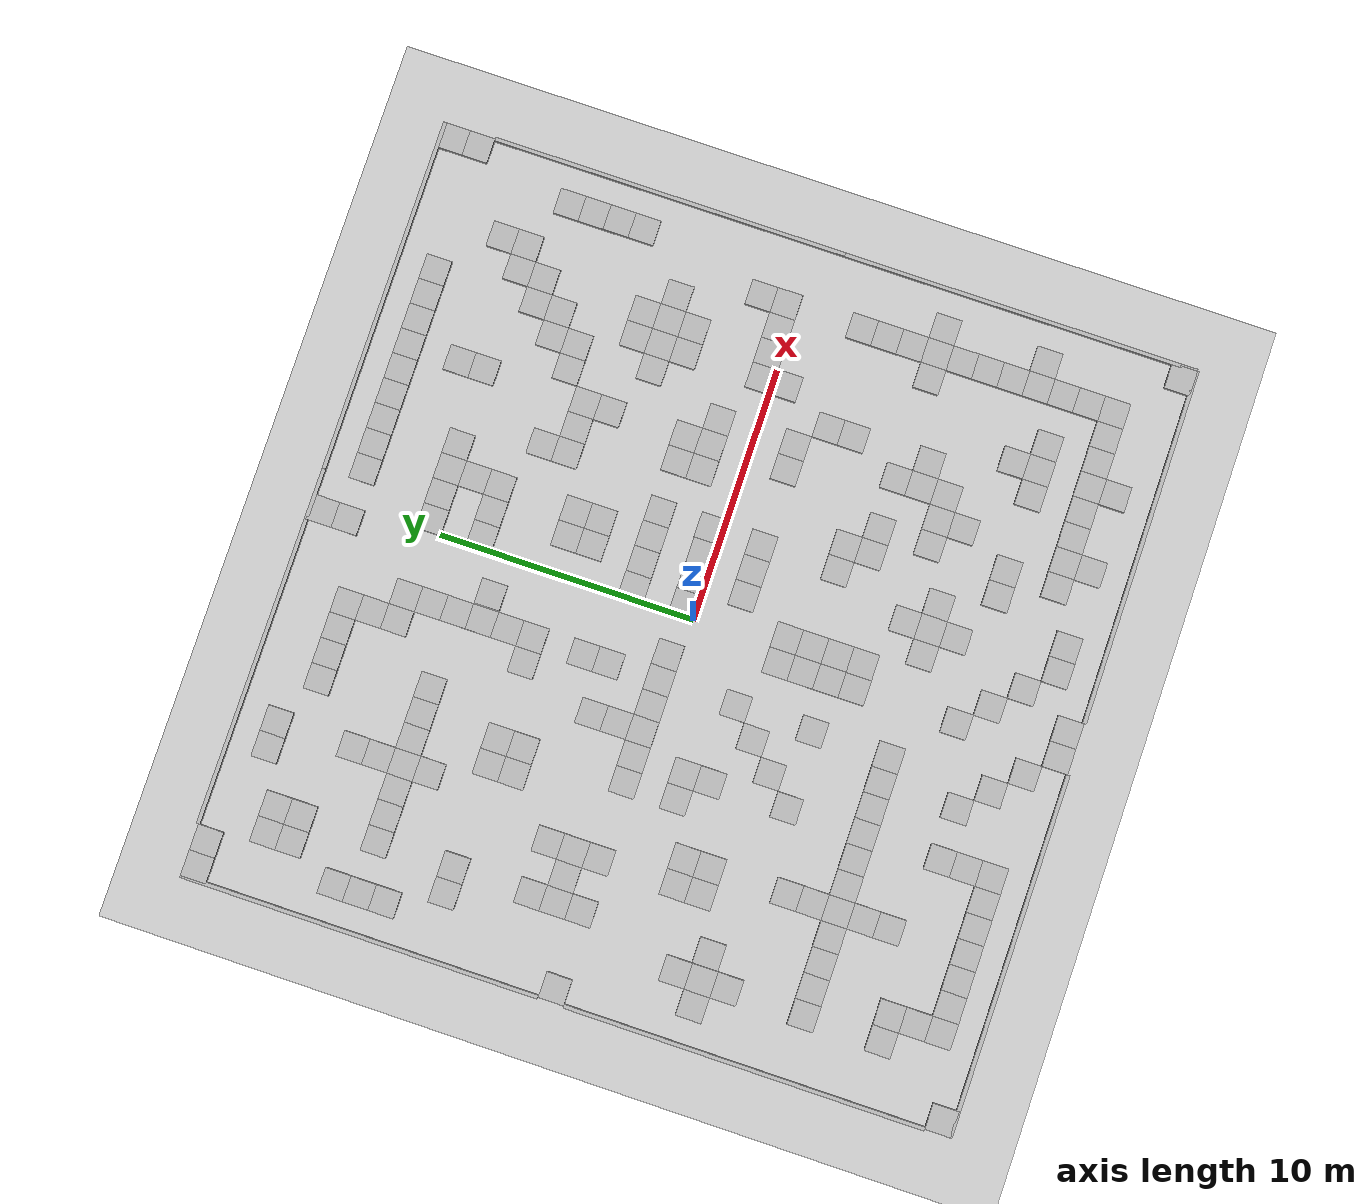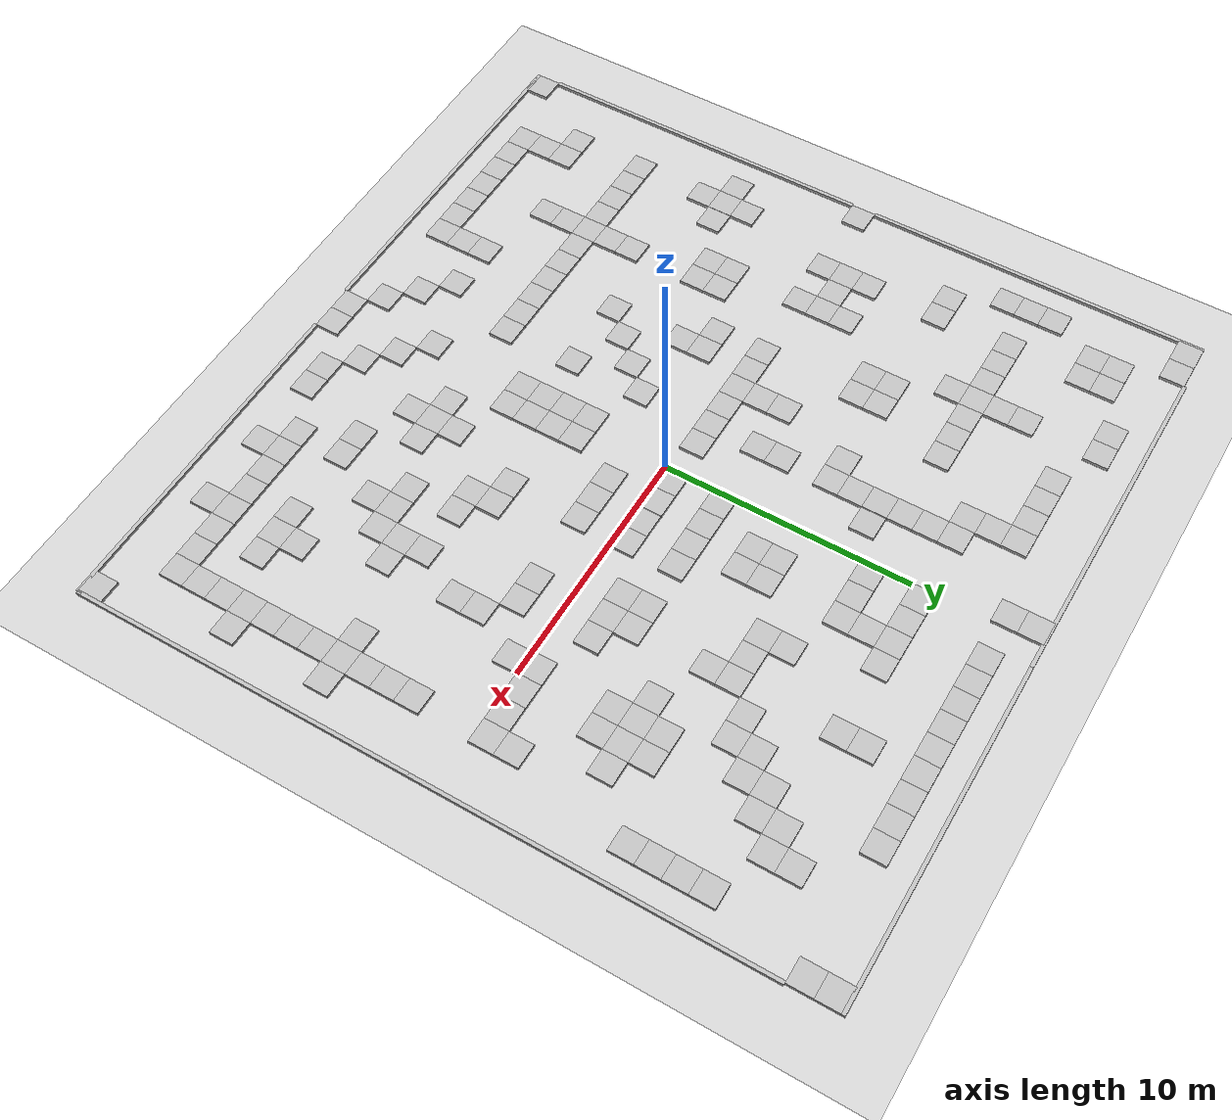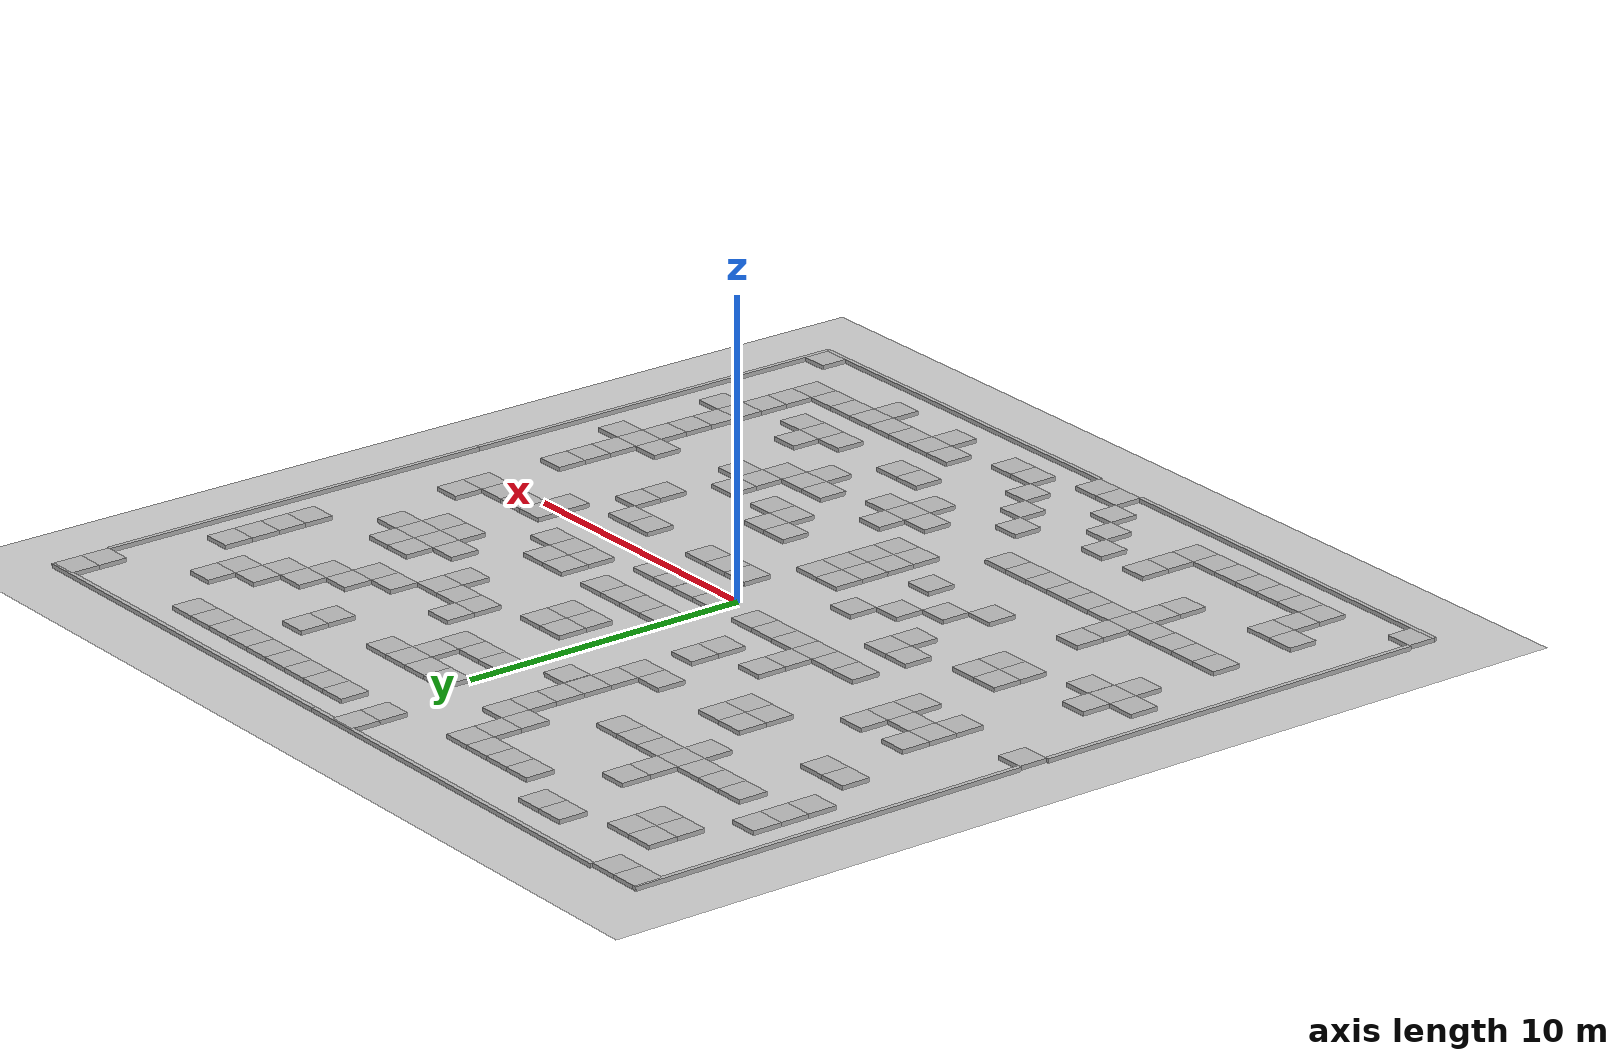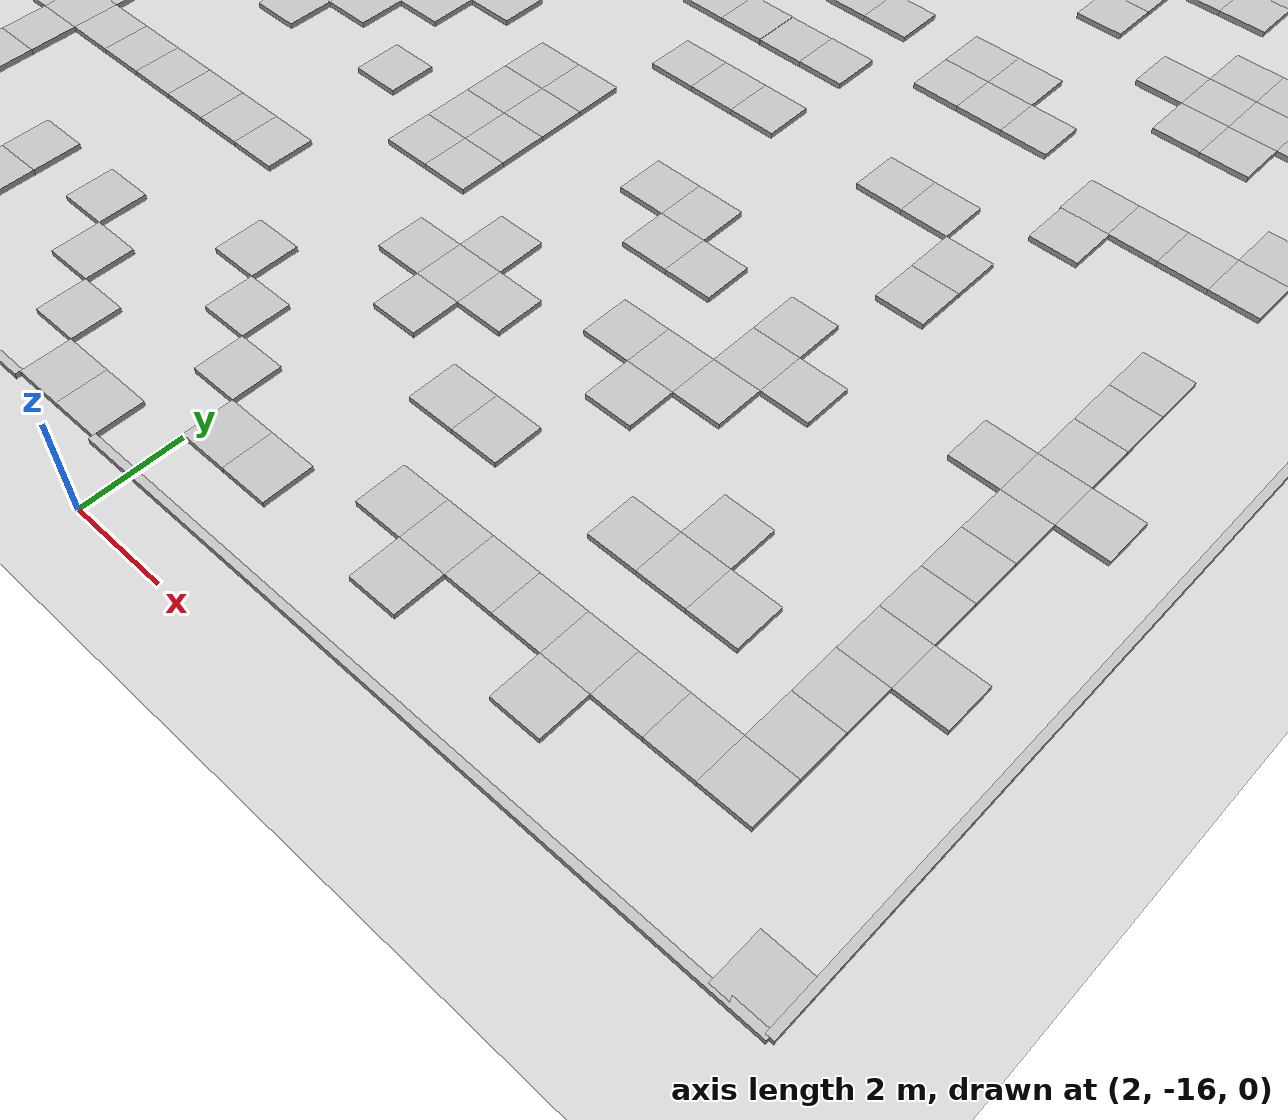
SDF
<sdf version="1.7">
 <world name="default">
  <light name="sun" type="directional">
   <pose>0 0 10 0 -0 0</pose>
   <diffuse>0.8 0.8 0.8 1</diffuse>
   <specular>0.2 0.2 0.2 1</specular>
   <attenuation>
    <range>1000</range>
    <constant>0.9</constant>
    <linear>0.01</linear>
    <quadratic>0.001</quadratic>
   </attenuation>
   <direction>-0.5 0.1 -0.9</direction>
   <spot><inner_angle>0</inner_angle><outer_angle>0</outer_angle><falloff>0</falloff></spot>
  </light>
  <model name="ground_plane">
   <static>1</static>
   <link name="link">
    <collision name="collision">
     <geometry><plane><normal>0 0 1</normal><size>100 100</size></plane></geometry>
     <surface>
      <contact><collide_bitmask>65535</collide_bitmask></contact>
      <friction><ode><mu>100</mu><mu2>50</mu2></ode></friction>
     </surface>
    </collision>
    <visual name="visual">
     <cast_shadows>0</cast_shadows>
     <geometry><plane><normal>0 0 1</normal><size>100 100</size></plane></geometry>
     <material>
      <script><uri>file://media/materials/scripts/gazebo.material</uri><name>Gazebo/Grey</name></script>
     </material>
    </visual>
   </link>
  </model>
  <gravity>0 0 -9.8</gravity>
  <magnetic_field>6e-06 2.3e-05 -4.2e-05</magnetic_field>
  <atmosphere type="adiabatic"/>
  <physics type="ode">
   <max_step_size>0.001</max_step_size>
   <real_time_factor>1</real_time_factor>
   <real_time_update_rate>1000</real_time_update_rate>
  </physics>
  <scene><ambient>0.4 0.4 0.4 1</ambient><background>0.7 0.7 0.7 1</background><shadows>1</shadows></scene>
  <spherical_coordinates>
   <surface_model>EARTH_WGS84</surface_model>
   <latitude_deg>0</latitude_deg>
   <longitude_deg>0</longitude_deg>
   <elevation>0</elevation>
   <heading_deg>0</heading_deg>
  </spherical_coordinates>
  <model name="concrete_barrier_14m">
   <static>1</static>
   <link name="link">
    <collision name="concrete_barrier_14m_01">
     <pose>-0 0 0.3 0 -0 0</pose>
     <geometry><box><size>14 0.15 0.6</size></box></geometry>
    </collision>
    <visual name="concrete_barrier_14m_visual">
     <geometry><mesh><uri>model://concrete_barrier_14m/meshes/concrete_barrier_14m.dae</uri></mesh></geometry>
    </visual>
   </link>
   <pose>-15 8 -3.1e-05 0 -0 0</pose>
  </model>
  <model name="concrete_barrier_14m_0">
   <static>1</static>
   <link name="link">
    <collision name="concrete_barrier_14m_01">
     <pose>-0 0 0.3 0 -0 0</pose>
     <geometry><box><size>14 0.15 0.6</size></box></geometry>
    </collision>
    <visual name="concrete_barrier_14m_visual">
     <geometry><mesh><uri>model://concrete_barrier_14m/meshes/concrete_barrier_14m.dae</uri></mesh></geometry>
    </visual>
   </link>
   <pose>15 6 0 0 -0 0</pose>
  </model>
  <model name="concrete_barrier_14m_2">
   <static>1</static>
   <link name="link">
    <collision name="concrete_barrier_14m_01">
     <pose>-0 0 0.3 0 -0 0</pose>
     <geometry><box><size>14 0.15 0.6</size></box></geometry>
    </collision>
    <visual name="concrete_barrier_14m_visual">
     <geometry><mesh><uri>model://concrete_barrier_14m/meshes/concrete_barrier_14m.dae</uri></mesh></geometry>
    </visual>
   </link>
   <pose>-15 -7 0 0 -0 0</pose>
  </model>
  <model name="concrete_barrier_14m_3">
   <static>1</static>
   <link name="link">
    <collision name="concrete_barrier_14m_01">
     <pose>-0 0 0.3 0 -0 0</pose>
     <geometry><box><size>14 0.15 0.6</size></box></geometry>
    </collision>
    <visual name="concrete_barrier_14m_visual">
     <geometry><mesh><uri>model://concrete_barrier_14m/meshes/concrete_barrier_14m.dae</uri></mesh></geometry>
    </visual>
   </link>
   <pose>15 -8 0 0 -0 0</pose>
  </model>
  <model name="concrete_barrier_14m_4">
   <static>1</static>
   <link name="link">
    <collision name="concrete_barrier_14m_01">
     <pose>-0 0 0.3 0 -0 0</pose>
     <geometry><box><size>14 0.15 0.6</size></box></geometry>
    </collision>
    <visual name="concrete_barrier_14m_visual">
     <geometry><mesh><uri>model://concrete_barrier_14m/meshes/concrete_barrier_14m.dae</uri></mesh></geometry>
    </visual>
   </link>
   <pose>8 15 0 0 0 -1.56953</pose>
  </model>
  <model name="concrete_barrier_14m_5">
   <static>1</static>
   <link name="link">
    <collision name="concrete_barrier_14m_01">
     <pose>-0 0 0.3 0 -0 0</pose>
     <geometry><box><size>14 0.15 0.6</size></box></geometry>
    </collision>
    <visual name="concrete_barrier_14m_visual">
     <geometry><mesh><uri>model://concrete_barrier_14m/meshes/concrete_barrier_14m.dae</uri></mesh></geometry>
    </visual>
   </link>
   <pose>-8 -15 0 0 -0 1.56737</pose>
  </model>
  <model name="concrete_barrier_14m_6">
   <static>1</static>
   <link name="link">
    <collision name="concrete_barrier_14m_01">
     <pose>-0 0 0.3 0 -0 0</pose>
     <geometry><box><size>14 0.15 0.6</size></box></geometry>
    </collision>
    <visual name="concrete_barrier_14m_visual">
     <geometry><mesh><uri>model://concrete_barrier_14m/meshes/concrete_barrier_14m.dae</uri></mesh></geometry>
    </visual>
   </link>
   <pose>8 -15 0 0 0 -1.56953</pose>
  </model>
  <model name="concrete_cube_1m">
   <static>1</static>
   <link name="link">
    <collision name="concrete_cube_1m">
     <pose>-0 0 0.3 0 -0 0</pose>
     <geometry><box><size>1 1 0.6</size></box></geometry>
    </collision>
    <visual name="concrete_cube_1m_visual">
     <geometry><mesh><uri>model://concrete_cube_1m/meshes/concrete_cube_1m.dae</uri></mesh></geometry>
    </visual>
   </link>
   <pose>-2.5 6.5 0 0 -0 0</pose>
  </model>
  <model name="concrete_cube_1m_0">
   <static>1</static>
   <link name="link">
    <collision name="concrete_cube_1m">
     <pose>-0 0 0.3 0 -0 0</pose>
     <geometry><box><size>1 1 0.6</size></box></geometry>
    </collision>
    <visual name="concrete_cube_1m_visual">
     <geometry><mesh><uri>model://concrete_cube_1m/meshes/concrete_cube_1m.dae</uri></mesh></geometry>
    </visual>
   </link>
   <pose>-6.5 4.5 0 0 -0 0</pose>
  </model>
  <model name="concrete_cube_1m_1">
   <static>1</static>
   <link name="link">
    <collision name="concrete_cube_1m">
     <pose>-0 0 0.3 0 -0 0</pose>
     <geometry><box><size>1 1 0.6</size></box></geometry>
    </collision>
    <visual name="concrete_cube_1m_visual">
     <geometry><mesh><uri>model://concrete_cube_1m/meshes/concrete_cube_1m.dae</uri></mesh></geometry>
    </visual>
   </link>
   <pose>-2.5 5.5 0 0 -0 0</pose>
  </model>
  <model name="concrete_cube_1m_2">
   <static>1</static>
   <link name="link">
    <collision name="concrete_cube_1m">
     <pose>-0 0 0.3 0 -0 0</pose>
     <geometry><box><size>1 1 0.6</size></box></geometry>
    </collision>
    <visual name="concrete_cube_1m_visual">
     <geometry><mesh><uri>model://concrete_cube_1m/meshes/concrete_cube_1m.dae</uri></mesh></geometry>
    </visual>
   </link>
   <pose>-1.5 0.5 0 0 -0 0</pose>
  </model>
  <model name="concrete_cube_1m_3">
   <static>1</static>
   <link name="link">
    <collision name="concrete_cube_1m">
     <pose>-0 0 0.3 0 -0 0</pose>
     <geometry><box><size>1 1 0.6</size></box></geometry>
    </collision>
    <visual name="concrete_cube_1m_visual">
     <geometry><mesh><uri>model://concrete_cube_1m/meshes/concrete_cube_1m.dae</uri></mesh></geometry>
    </visual>
   </link>
   <pose>-4.5 0.5 0 0 -0 0</pose>
  </model>
  <model name="concrete_cube_1m_4">
   <static>1</static>
   <link name="link">
    <collision name="concrete_cube_1m">
     <pose>-0 0 0.3 0 -0 0</pose>
     <geometry><box><size>1 1 0.6</size></box></geometry>
    </collision>
    <visual name="concrete_cube_1m_visual">
     <geometry><mesh><uri>model://concrete_cube_1m/meshes/concrete_cube_1m.dae</uri></mesh></geometry>
    </visual>
   </link>
   <pose>6.5 2.5 0 0 -0 0</pose>
  </model>
  <model name="concrete_cube_1m_5">
   <static>1</static>
   <link name="link">
    <collision name="concrete_cube_1m">
     <pose>-0 0 0.3 0 -0 0</pose>
     <geometry><box><size>1 1 0.6</size></box></geometry>
    </collision>
    <visual name="concrete_cube_1m_visual">
     <geometry><mesh><uri>model://concrete_cube_1m/meshes/concrete_cube_1m.dae</uri></mesh></geometry>
    </visual>
   </link>
   <pose>5.5 2.5 0 0 -0 0</pose>
  </model>
  <model name="concrete_cube_1m_6">
   <static>1</static>
   <link name="link">
    <collision name="concrete_cube_1m">
     <pose>-0 0 0.3 0 -0 0</pose>
     <geometry><box><size>1 1 0.6</size></box></geometry>
    </collision>
    <visual name="concrete_cube_1m_visual">
     <geometry><mesh><uri>model://concrete_cube_1m/meshes/concrete_cube_1m.dae</uri></mesh></geometry>
    </visual>
   </link>
   <pose>6.5 1.5 0 0 -0 0</pose>
  </model>
  <model name="concrete_cube_1m_7">
   <static>1</static>
   <link name="link">
    <collision name="concrete_cube_1m">
     <pose>-0 0 0.3 0 -0 0</pose>
     <geometry><box><size>1 1 0.6</size></box></geometry>
    </collision>
    <visual name="concrete_cube_1m_visual">
     <geometry><mesh><uri>model://concrete_cube_1m/meshes/concrete_cube_1m.dae</uri></mesh></geometry>
    </visual>
   </link>
   <pose>5.5 1.5 0 0 -0 0</pose>
  </model>
  <model name="concrete_cube_1m_8">
   <static>1</static>
   <link name="link">
    <collision name="concrete_cube_1m">
     <pose>-0 0 0.3 0 -0 0</pose>
     <geometry><box><size>1 1 0.6</size></box></geometry>
    </collision>
    <visual name="concrete_cube_1m_visual">
     <geometry><mesh><uri>model://concrete_cube_1m/meshes/concrete_cube_1m.dae</uri></mesh></geometry>
    </visual>
   </link>
   <pose>-0.5 -4.5 0 0 -0 0</pose>
  </model>
  <model name="concrete_cube_1m_9">
   <static>1</static>
   <link name="link">
    <collision name="concrete_cube_1m">
     <pose>-0 0 0.3 0 -0 0</pose>
     <geometry><box><size>1 1 0.6</size></box></geometry>
    </collision>
    <visual name="concrete_cube_1m_visual">
     <geometry><mesh><uri>model://concrete_cube_1m/meshes/concrete_cube_1m.dae</uri></mesh></geometry>
    </visual>
   </link>
   <pose>0.5 -4.5 0 0 -0 0</pose>
  </model>
  <model name="concrete_cube_1m_10">
   <static>1</static>
   <link name="link">
    <collision name="concrete_cube_1m">
     <pose>-0 0 0.3 0 -0 0</pose>
     <geometry><box><size>1 1 0.6</size></box></geometry>
    </collision>
    <visual name="concrete_cube_1m_visual">
     <geometry><mesh><uri>model://concrete_cube_1m/meshes/concrete_cube_1m.dae</uri></mesh></geometry>
    </visual>
   </link>
   <pose>4.5 -5.5 0 0 -0 0</pose>
  </model>
  <model name="concrete_cube_1m_11">
   <static>1</static>
   <link name="link">
    <collision name="concrete_cube_1m">
     <pose>-0 0 0.3 0 -0 0</pose>
     <geometry><box><size>1 1 0.6</size></box></geometry>
    </collision>
    <visual name="concrete_cube_1m_visual">
     <geometry><mesh><uri>model://concrete_cube_1m/meshes/concrete_cube_1m.dae</uri></mesh></geometry>
    </visual>
   </link>
   <pose>5.5 -5.5 0 0 -0 0</pose>
  </model>
  <model name="concrete_cube_1m_12">
   <static>1</static>
   <link name="link">
    <collision name="concrete_cube_1m">
     <pose>-0 0 0.3 0 -0 0</pose>
     <geometry><box><size>1 1 0.6</size></box></geometry>
    </collision>
    <visual name="concrete_cube_1m_visual">
     <geometry><mesh><uri>model://concrete_cube_1m/meshes/concrete_cube_1m.dae</uri></mesh></geometry>
    </visual>
   </link>
   <pose>-8.5 -8.5 0 0 -0 0</pose>
  </model>
  <model name="concrete_cube_1m_13">
   <static>1</static>
   <link name="link">
    <collision name="concrete_cube_1m">
     <pose>-0 0 0.3 0 -0 0</pose>
     <geometry><box><size>1 1 0.6</size></box></geometry>
    </collision>
    <visual name="concrete_cube_1m_visual">
     <geometry><mesh><uri>model://concrete_cube_1m/meshes/concrete_cube_1m.dae</uri></mesh></geometry>
    </visual>
   </link>
   <pose>-7.5 -8.5 0 0 -0 0</pose>
  </model>
  <model name="concrete_cube_1m_14">
   <static>1</static>
   <link name="link">
    <collision name="concrete_cube_1m">
     <pose>-0 0 0.3 0 -0 0</pose>
     <geometry><box><size>1 1 0.6</size></box></geometry>
    </collision>
    <visual name="concrete_cube_1m_visual">
     <geometry><mesh><uri>model://concrete_cube_1m/meshes/concrete_cube_1m.dae</uri></mesh></geometry>
    </visual>
   </link>
   <pose>-6.5 -8.5 0 0 -0 0</pose>
  </model>
  <model name="concrete_cube_1m_15">
   <static>1</static>
   <link name="link">
    <collision name="concrete_cube_1m">
     <pose>-0 0 0.3 0 -0 0</pose>
     <geometry><box><size>1 1 0.6</size></box></geometry>
    </collision>
    <visual name="concrete_cube_1m_visual">
     <geometry><mesh><uri>model://concrete_cube_1m/meshes/concrete_cube_1m.dae</uri></mesh></geometry>
    </visual>
   </link>
   <pose>-8.5 -7.5 0 0 -0 0</pose>
  </model>
  <model name="concrete_cube_1m_16">
   <static>1</static>
   <link name="link">
    <collision name="concrete_cube_1m">
     <pose>-0 0 0.3 0 -0 0</pose>
     <geometry><box><size>1 1 0.6</size></box></geometry>
    </collision>
    <visual name="concrete_cube_1m_visual">
     <geometry><mesh><uri>model://concrete_cube_1m/meshes/concrete_cube_1m.dae</uri></mesh></geometry>
    </visual>
   </link>
   <pose>-8.5 -6.5 0 0 -0 0</pose>
  </model>
  <model name="concrete_cube_1m_17">
   <static>1</static>
   <link name="link">
    <collision name="concrete_cube_1m">
     <pose>-0 0 0.3 0 -0 0</pose>
     <geometry><box><size>1 1 0.6</size></box></geometry>
    </collision>
    <visual name="concrete_cube_1m_visual">
     <geometry><mesh><uri>model://concrete_cube_1m/meshes/concrete_cube_1m.dae</uri></mesh></geometry>
    </visual>
   </link>
   <pose>2.5 5.5 0 0 -0 0</pose>
  </model>
  <model name="concrete_cube_1m_18">
   <static>1</static>
   <link name="link">
    <collision name="concrete_cube_1m">
     <pose>-0 0 0.3 0 -0 0</pose>
     <geometry><box><size>1 1 0.6</size></box></geometry>
    </collision>
    <visual name="concrete_cube_1m_visual">
     <geometry><mesh><uri>model://concrete_cube_1m/meshes/concrete_cube_1m.dae</uri></mesh></geometry>
    </visual>
   </link>
   <pose>8.5 8.5 0 0 -0 0</pose>
  </model>
  <model name="concrete_cube_1m_19">
   <static>1</static>
   <link name="link">
    <collision name="concrete_cube_1m">
     <pose>-0 0 0.3 0 -0 0</pose>
     <geometry><box><size>1 1 0.6</size></box></geometry>
    </collision>
    <visual name="concrete_cube_1m_visual">
     <geometry><mesh><uri>model://concrete_cube_1m/meshes/concrete_cube_1m.dae</uri></mesh></geometry>
    </visual>
   </link>
   <pose>7.5 7.5 0 0 -0 0</pose>
  </model>
  <model name="concrete_cube_1m_20">
   <static>1</static>
   <link name="link">
    <collision name="concrete_cube_1m">
     <pose>-0 0 0.3 0 -0 0</pose>
     <geometry><box><size>1 1 0.6</size></box></geometry>
    </collision>
    <visual name="concrete_cube_1m_visual">
     <geometry><mesh><uri>model://concrete_cube_1m/meshes/concrete_cube_1m.dae</uri></mesh></geometry>
    </visual>
   </link>
   <pose>6.5 6.5 0 0 -0 0</pose>
  </model>
  <model name="concrete_cube_1m_21">
   <static>1</static>
   <link name="link">
    <collision name="concrete_cube_1m">
     <pose>-0 0 0.3 0 -0 0</pose>
     <geometry><box><size>1 1 0.6</size></box></geometry>
    </collision>
    <visual name="concrete_cube_1m_visual">
     <geometry><mesh><uri>model://concrete_cube_1m/meshes/concrete_cube_1m.dae</uri></mesh></geometry>
    </visual>
   </link>
   <pose>6.5 5.5 0 0 -0 0</pose>
  </model>
  <model name="concrete_cube_1m_22">
   <static>1</static>
   <link name="link">
    <collision name="concrete_cube_1m">
     <pose>-0 0 0.3 0 -0 0</pose>
     <geometry><box><size>1 1 0.6</size></box></geometry>
    </collision>
    <visual name="concrete_cube_1m_visual">
     <geometry><mesh><uri>model://concrete_cube_1m/meshes/concrete_cube_1m.dae</uri></mesh></geometry>
    </visual>
   </link>
   <pose>5.5 6.5 0 0 -0 0</pose>
  </model>
  <model name="concrete_cube_1m_23">
   <static>1</static>
   <link name="link">
    <collision name="concrete_cube_1m">
     <pose>-0 0 0.3 0 -0 0</pose>
     <geometry><box><size>1 1 0.6</size></box></geometry>
    </collision>
    <visual name="concrete_cube_1m_visual">
     <geometry><mesh><uri>model://concrete_cube_1m/meshes/concrete_cube_1m.dae</uri></mesh></geometry>
    </visual>
   </link>
   <pose>4.5 6.5 0 0 -0 0</pose>
  </model>
  <model name="concrete_cube_1m_24">
   <static>1</static>
   <link name="link">
    <collision name="concrete_cube_1m">
     <pose>-0 0 0.3 0 -0 0</pose>
     <geometry><box><size>1 1 0.6</size></box></geometry>
    </collision>
    <visual name="concrete_cube_1m_visual">
     <geometry><mesh><uri>model://concrete_cube_1m/meshes/concrete_cube_1m.dae</uri></mesh></geometry>
    </visual>
   </link>
   <pose>4.5 7.5 0 0 -0 0</pose>
  </model>
  <model name="concrete_cube_1m_25">
   <static>1</static>
   <link name="link">
    <collision name="concrete_cube_1m">
     <pose>-0 0 0.3 0 -0 0</pose>
     <geometry><box><size>1 1 0.6</size></box></geometry>
    </collision>
    <visual name="concrete_cube_1m_visual">
     <geometry><mesh><uri>model://concrete_cube_1m/meshes/concrete_cube_1m.dae</uri></mesh></geometry>
    </visual>
   </link>
   <pose>3.5 2.5 0 0 -0 0</pose>
  </model>
  <model name="concrete_cube_1m_26">
   <static>1</static>
   <link name="link">
    <collision name="concrete_cube_1m">
     <pose>-0 0 0.3 0 -0 0</pose>
     <geometry><box><size>1 1 0.6</size></box></geometry>
    </collision>
    <visual name="concrete_cube_1m_visual">
     <geometry><mesh><uri>model://concrete_cube_1m/meshes/concrete_cube_1m.dae</uri></mesh></geometry>
    </visual>
   </link>
   <pose>2.5 2.5 0 0 -0 0</pose>
  </model>
  <model name="concrete_cube_1m_27">
   <static>1</static>
   <link name="link">
    <collision name="concrete_cube_1m">
     <pose>-0 0 0.3 0 -0 0</pose>
     <geometry><box><size>1 1 0.6</size></box></geometry>
    </collision>
    <visual name="concrete_cube_1m_visual">
     <geometry><mesh><uri>model://concrete_cube_1m/meshes/concrete_cube_1m.dae</uri></mesh></geometry>
    </visual>
   </link>
   <pose>1.5 2.5 0 0 -0 0</pose>
  </model>
  <model name="concrete_cube_1m_28">
   <static>1</static>
   <link name="link">
    <collision name="concrete_cube_1m">
     <pose>-0 0 0.3 0 -0 0</pose>
     <geometry><box><size>1 1 0.6</size></box></geometry>
    </collision>
    <visual name="concrete_cube_1m_visual">
     <geometry><mesh><uri>model://concrete_cube_1m/meshes/concrete_cube_1m.dae</uri></mesh></geometry>
    </visual>
   </link>
   <pose>0.5 2.5 0 0 -0 0</pose>
  </model>
  <model name="concrete_cube_1m_29">
   <static>1</static>
   <link name="link">
    <collision name="concrete_cube_1m">
     <pose>-0 0 0.3 0 -0 0</pose>
     <geometry><box><size>1 1 0.6</size></box></geometry>
    </collision>
    <visual name="concrete_cube_1m_visual">
     <geometry><mesh><uri>model://concrete_cube_1m/meshes/concrete_cube_1m.dae</uri></mesh></geometry>
    </visual>
   </link>
   <pose>1.5 4.5 0 0 -0 0</pose>
  </model>
  <model name="concrete_cube_1m_30">
   <static>1</static>
   <link name="link">
    <collision name="concrete_cube_1m">
     <pose>-0 0 0.3 0 -0 0</pose>
     <geometry><box><size>1 1 0.6</size></box></geometry>
    </collision>
    <visual name="concrete_cube_1m_visual">
     <geometry><mesh><uri>model://concrete_cube_1m/meshes/concrete_cube_1m.dae</uri></mesh></geometry>
    </visual>
   </link>
   <pose>8.5 4.5 0 0 -0 0</pose>
  </model>
  <model name="concrete_cube_1m_31">
   <static>1</static>
   <link name="link">
    <collision name="concrete_cube_1m">
     <pose>-0 0 0.3 0 -0 0</pose>
     <geometry><box><size>1 1 0.6</size></box></geometry>
    </collision>
    <visual name="concrete_cube_1m_visual">
     <geometry><mesh><uri>model://concrete_cube_1m/meshes/concrete_cube_1m.dae</uri></mesh></geometry>
    </visual>
   </link>
   <pose>9.5 4.5 0 0 -0 0</pose>
  </model>
  <model name="concrete_cube_1m_32">
   <static>1</static>
   <link name="link">
    <collision name="concrete_cube_1m">
     <pose>-0 0 0.3 0 -0 0</pose>
     <geometry><box><size>1 1 0.6</size></box></geometry>
    </collision>
    <visual name="concrete_cube_1m_visual">
     <geometry><mesh><uri>model://concrete_cube_1m/meshes/concrete_cube_1m.dae</uri></mesh></geometry>
    </visual>
   </link>
   <pose>9.5 3.5 0 0 -0 0</pose>
  </model>
  <model name="concrete_cube_1m_33">
   <static>1</static>
   <link name="link">
    <collision name="concrete_cube_1m">
     <pose>-0 0 0.3 0 -0 0</pose>
     <geometry><box><size>1 1 0.6</size></box></geometry>
    </collision>
    <visual name="concrete_cube_1m_visual">
     <geometry><mesh><uri>model://concrete_cube_1m/meshes/concrete_cube_1m.dae</uri></mesh></geometry>
    </visual>
   </link>
   <pose>9.5 5.5 0 0 -0 0</pose>
  </model>
  <model name="concrete_cube_1m_34">
   <static>1</static>
   <link name="link">
    <collision name="concrete_cube_1m">
     <pose>-0 0 0.3 0 -0 0</pose>
     <geometry><box><size>1 1 0.6</size></box></geometry>
    </collision>
    <visual name="concrete_cube_1m_visual">
     <geometry><mesh><uri>model://concrete_cube_1m/meshes/concrete_cube_1m.dae</uri></mesh></geometry>
    </visual>
   </link>
   <pose>7.5 1.5 0 0 -0 0</pose>
  </model>
  <model name="concrete_cube_1m_35">
   <static>1</static>
   <link name="link">
    <collision name="concrete_cube_1m">
     <pose>-0 0 0.3 0 -0 0</pose>
     <geometry><box><size>1 1 0.6</size></box></geometry>
    </collision>
    <visual name="concrete_cube_1m_visual">
     <geometry><mesh><uri>model://concrete_cube_1m/meshes/concrete_cube_1m.dae</uri></mesh></geometry>
    </visual>
   </link>
   <pose>9.5 0.5 0 0 -0 0</pose>
  </model>
  <model name="concrete_cube_1m_36">
   <static>1</static>
   <link name="link">
    <collision name="concrete_cube_1m">
     <pose>-0 0 0.3 0 -0 0</pose>
     <geometry><box><size>1 1 0.6</size></box></geometry>
    </collision>
    <visual name="concrete_cube_1m_visual">
     <geometry><mesh><uri>model://concrete_cube_1m/meshes/concrete_cube_1m.dae</uri></mesh></geometry>
    </visual>
   </link>
   <pose>2.5 8.5 0 0 -0 0</pose>
  </model>
  <model name="concrete_cube_1m_37">
   <static>1</static>
   <link name="link">
    <collision name="concrete_cube_1m">
     <pose>-0 0 0.3 0 -0 0</pose>
     <geometry><box><size>1 1 0.6</size></box></geometry>
    </collision>
    <visual name="concrete_cube_1m_visual">
     <geometry><mesh><uri>model://concrete_cube_1m/meshes/concrete_cube_1m.dae</uri></mesh></geometry>
    </visual>
   </link>
   <pose>1.5 8.5 0 0 -0 0</pose>
  </model>
  <model name="concrete_cube_1m_38">
   <static>1</static>
   <link name="link">
    <collision name="concrete_cube_1m">
     <pose>-0 0 0.3 0 -0 0</pose>
     <geometry><box><size>1 1 0.6</size></box></geometry>
    </collision>
    <visual name="concrete_cube_1m_visual">
     <geometry><mesh><uri>model://concrete_cube_1m/meshes/concrete_cube_1m.dae</uri></mesh></geometry>
    </visual>
   </link>
   <pose>0.5 8.5 0 0 -0 0</pose>
  </model>
  <model name="concrete_cube_1m_39">
   <static>1</static>
   <link name="link">
    <collision name="concrete_cube_1m">
     <pose>-0 0 0.3 0 -0 0</pose>
     <geometry><box><size>1 1 0.6</size></box></geometry>
    </collision>
    <visual name="concrete_cube_1m_visual">
     <geometry><mesh><uri>model://concrete_cube_1m/meshes/concrete_cube_1m.dae</uri></mesh></geometry>
    </visual>
   </link>
   <pose>2.5 4.5 0 0 -0 0</pose>
  </model>
  <model name="concrete_cube_1m_40">
   <static>1</static>
   <link name="link">
    <collision name="concrete_cube_1m">
     <pose>-0 0 0.3 0 -0 0</pose>
     <geometry><box><size>1 1 0.6</size></box></geometry>
    </collision>
    <visual name="concrete_cube_1m_visual">
     <geometry><mesh><uri>model://concrete_cube_1m/meshes/concrete_cube_1m.dae</uri></mesh></geometry>
    </visual>
   </link>
   <pose>1.5 5.5 0 0 -0 0</pose>
  </model>
  <model name="concrete_cube_1m_41">
   <static>1</static>
   <link name="link">
    <collision name="concrete_cube_1m">
     <pose>-0 0 0.3 0 -0 0</pose>
     <geometry><box><size>1 1 0.6</size></box></geometry>
    </collision>
    <visual name="concrete_cube_1m_visual">
     <geometry><mesh><uri>model://concrete_cube_1m/meshes/concrete_cube_1m.dae</uri></mesh></geometry>
    </visual>
   </link>
   <pose>3.5 0.5 0 0 -0 0</pose>
  </model>
  <model name="concrete_cube_1m_42">
   <static>1</static>
   <link name="link">
    <collision name="concrete_cube_1m">
     <pose>-0 0 0.3 0 -0 0</pose>
     <geometry><box><size>1 1 0.6</size></box></geometry>
    </collision>
    <visual name="concrete_cube_1m_visual">
     <geometry><mesh><uri>model://concrete_cube_1m/meshes/concrete_cube_1m.dae</uri></mesh></geometry>
    </visual>
   </link>
   <pose>2.51365 0.491319 0 0 -0 0</pose>
  </model>
  <model name="concrete_cube_1m_43">
   <static>1</static>
   <link name="link">
    <collision name="concrete_cube_1m">
     <pose>-0 0 0.3 0 -0 0</pose>
     <geometry><box><size>1 1 0.6</size></box></geometry>
    </collision>
    <visual name="concrete_cube_1m_visual">
     <geometry><mesh><uri>model://concrete_cube_1m/meshes/concrete_cube_1m.dae</uri></mesh></geometry>
    </visual>
   </link>
   <pose>-3.5 5.5 0 0 -0 0</pose>
  </model>
  <model name="concrete_cube_1m_44">
   <static>1</static>
   <link name="link">
    <collision name="concrete_cube_1m">
     <pose>-0 0 0.3 0 -0 0</pose>
     <geometry><box><size>1 1 0.6</size></box></geometry>
    </collision>
    <visual name="concrete_cube_1m_visual">
     <geometry><mesh><uri>model://concrete_cube_1m/meshes/concrete_cube_1m.dae</uri></mesh></geometry>
    </visual>
   </link>
   <pose>-2.5 7.5 0 0 -0 0</pose>
  </model>
  <model name="concrete_cube_1m_45">
   <static>1</static>
   <link name="link">
    <collision name="concrete_cube_1m">
     <pose>-0 0 0.3 0 -0 0</pose>
     <geometry><box><size>1 1 0.6</size></box></geometry>
    </collision>
    <visual name="concrete_cube_1m_visual">
     <geometry><mesh><uri>model://concrete_cube_1m/meshes/concrete_cube_1m.dae</uri></mesh></geometry>
    </visual>
   </link>
   <pose>-2.5 0.5 0 0 -0 0</pose>
  </model>
  <model name="concrete_cube_1m_46">
   <static>1</static>
   <link name="link">
    <collision name="concrete_cube_1m">
     <pose>-0 0 0.3 0 -0 0</pose>
     <geometry><box><size>1 1 0.6</size></box></geometry>
    </collision>
    <visual name="concrete_cube_1m_visual">
     <geometry><mesh><uri>model://concrete_cube_1m/meshes/concrete_cube_1m.dae</uri></mesh></geometry>
    </visual>
   </link>
   <pose>-3.5 0.5 0 0 -0 0</pose>
  </model>
  <model name="concrete_cube_1m_47">
   <static>1</static>
   <link name="link">
    <collision name="concrete_cube_1m">
     <pose>-0 0 0.3 0 -0 0</pose>
     <geometry><box><size>1 1 0.6</size></box></geometry>
    </collision>
    <visual name="concrete_cube_1m_visual">
     <geometry><mesh><uri>model://concrete_cube_1m/meshes/concrete_cube_1m.dae</uri></mesh></geometry>
    </visual>
   </link>
   <pose>-4.5 1.5 0 0 -0 0</pose>
  </model>
  <model name="concrete_cube_1m_48">
   <static>1</static>
   <link name="link">
    <collision name="concrete_cube_1m">
     <pose>-0 0 0.3 0 -0 0</pose>
     <geometry><box><size>1 1 0.6</size></box></geometry>
    </collision>
    <visual name="concrete_cube_1m_visual">
     <geometry><mesh><uri>model://concrete_cube_1m/meshes/concrete_cube_1m.dae</uri></mesh></geometry>
    </visual>
   </link>
   <pose>-4.5 2.5 0 0 -0 0</pose>
  </model>
  <model name="concrete_cube_1m_49">
   <static>1</static>
   <link name="link">
    <collision name="concrete_cube_1m">
     <pose>-0 0 0.3 0 -0 0</pose>
     <geometry><box><size>1 1 0.6</size></box></geometry>
    </collision>
    <visual name="concrete_cube_1m_visual">
     <geometry><mesh><uri>model://concrete_cube_1m/meshes/concrete_cube_1m.dae</uri></mesh></geometry>
    </visual>
   </link>
   <pose>-5.5 0.5 0 0 -0 0</pose>
  </model>
  <model name="concrete_cube_1m_50">
   <static>1</static>
   <link name="link">
    <collision name="concrete_cube_1m">
     <pose>-0 0 0.3 0 -0 0</pose>
     <geometry><box><size>1 1 0.6</size></box></geometry>
    </collision>
    <visual name="concrete_cube_1m_visual">
     <geometry><mesh><uri>model://concrete_cube_1m/meshes/concrete_cube_1m.dae</uri></mesh></geometry>
    </visual>
   </link>
   <pose>-6.5 0.5 0 0 -0 0</pose>
  </model>
  <model name="concrete_cube_1m_51">
   <static>1</static>
   <link name="link">
    <collision name="concrete_cube_1m">
     <pose>-0 0 0.3 0 -0 0</pose>
     <geometry><box><size>1 1 0.6</size></box></geometry>
    </collision>
    <visual name="concrete_cube_1m_visual">
     <geometry><mesh><uri>model://concrete_cube_1m/meshes/concrete_cube_1m.dae</uri></mesh></geometry>
    </visual>
   </link>
   <pose>-6.5 5.5 0 0 -0 0</pose>
  </model>
  <model name="concrete_cube_1m_52">
   <static>1</static>
   <link name="link">
    <collision name="concrete_cube_1m">
     <pose>-0 0 0.3 0 -0 0</pose>
     <geometry><box><size>1 1 0.6</size></box></geometry>
    </collision>
    <visual name="concrete_cube_1m_visual">
     <geometry><mesh><uri>model://concrete_cube_1m/meshes/concrete_cube_1m.dae</uri></mesh></geometry>
    </visual>
   </link>
   <pose>-7.5 4.5 0 0 -0 0</pose>
  </model>
  <model name="concrete_cube_1m_53">
   <static>1</static>
   <link name="link">
    <collision name="concrete_cube_1m">
     <pose>-0 0 0.3 0 -0 0</pose>
     <geometry><box><size>1 1 0.6</size></box></geometry>
    </collision>
    <visual name="concrete_cube_1m_visual">
     <geometry><mesh><uri>model://concrete_cube_1m/meshes/concrete_cube_1m.dae</uri></mesh></geometry>
    </visual>
   </link>
   <pose>-7.5 5.5 0 0 -0 0</pose>
  </model>
  <model name="concrete_cube_1m_54">
   <static>1</static>
   <link name="link">
    <collision name="concrete_cube_1m">
     <pose>-0 0 0.3 0 -0 0</pose>
     <geometry><box><size>1 1 0.6</size></box></geometry>
    </collision>
    <visual name="concrete_cube_1m_visual">
     <geometry><mesh><uri>model://concrete_cube_1m/meshes/concrete_cube_1m.dae</uri></mesh></geometry>
    </visual>
   </link>
   <pose>-8.5 8.5 0 0 -0 0</pose>
  </model>
  <model name="concrete_cube_1m_55">
   <static>1</static>
   <link name="link">
    <collision name="concrete_cube_1m">
     <pose>-0 0 0.3 0 -0 0</pose>
     <geometry><box><size>1 1 0.6</size></box></geometry>
    </collision>
    <visual name="concrete_cube_1m_visual">
     <geometry><mesh><uri>model://concrete_cube_1m/meshes/concrete_cube_1m.dae</uri></mesh></geometry>
    </visual>
   </link>
   <pose>-8.5 7.5 0 0 -0 0</pose>
  </model>
  <model name="concrete_cube_1m_56">
   <static>1</static>
   <link name="link">
    <collision name="concrete_cube_1m">
     <pose>-0 0 0.3 0 -0 0</pose>
     <geometry><box><size>1 1 0.6</size></box></geometry>
    </collision>
    <visual name="concrete_cube_1m_visual">
     <geometry><mesh><uri>model://concrete_cube_1m/meshes/concrete_cube_1m.dae</uri></mesh></geometry>
    </visual>
   </link>
   <pose>-7.5 8.5 0 0 -0 0</pose>
  </model>
  <model name="concrete_cube_1m_57">
   <static>1</static>
   <link name="link">
    <collision name="concrete_cube_1m">
     <pose>-0 0 0.3 0 -0 0</pose>
     <geometry><box><size>1 1 0.6</size></box></geometry>
    </collision>
    <visual name="concrete_cube_1m_visual">
     <geometry><mesh><uri>model://concrete_cube_1m/meshes/concrete_cube_1m.dae</uri></mesh></geometry>
    </visual>
   </link>
   <pose>-6.50041 8.5 0 0 -0 0</pose>
  </model>
  <model name="concrete_cube_1m_58">
   <static>1</static>
   <link name="link">
    <collision name="concrete_cube_1m">
     <pose>-0 0 0.3 0 -0 0</pose>
     <geometry><box><size>1 1 0.6</size></box></geometry>
    </collision>
    <visual name="concrete_cube_1m_visual">
     <geometry><mesh><uri>model://concrete_cube_1m/meshes/concrete_cube_1m.dae</uri></mesh></geometry>
    </visual>
   </link>
   <pose>-5.5 8.5 0 0 -0 0</pose>
  </model>
  <model name="concrete_cube_1m_59">
   <static>1</static>
   <link name="link">
    <collision name="concrete_cube_1m">
     <pose>-0 0 0.3 0 -0 0</pose>
     <geometry><box><size>1 1 0.6</size></box></geometry>
    </collision>
    <visual name="concrete_cube_1m_visual">
     <geometry><mesh><uri>model://concrete_cube_1m/meshes/concrete_cube_1m.dae</uri></mesh></geometry>
    </visual>
   </link>
   <pose>-1.46855 7.49755 0 0 -0 0</pose>
  </model>
  <model name="concrete_cube_1m_60">
   <static>1</static>
   <link name="link">
    <collision name="concrete_cube_1m">
     <pose>-0 0 0.3 0 -0 0</pose>
     <geometry><box><size>1 1 0.6</size></box></geometry>
    </collision>
    <visual name="concrete_cube_1m_visual">
     <geometry><mesh><uri>model://concrete_cube_1m/meshes/concrete_cube_1m.dae</uri></mesh></geometry>
    </visual>
   </link>
   <pose>-9.5 1.5 0 0 -0 0</pose>
  </model>
  <model name="concrete_cube_1m_61">
   <static>1</static>
   <link name="link">
    <collision name="concrete_cube_1m">
     <pose>-0 0 0.3 0 -0 0</pose>
     <geometry><box><size>1 1 0.6</size></box></geometry>
    </collision>
    <visual name="concrete_cube_1m_visual">
     <geometry><mesh><uri>model://concrete_cube_1m/meshes/concrete_cube_1m.dae</uri></mesh></geometry>
    </visual>
   </link>
   <pose>-9.5 2.5 0 0 -0 0</pose>
  </model>
  <model name="concrete_cube_1m_62">
   <static>1</static>
   <link name="link">
    <collision name="concrete_cube_1m">
     <pose>-0 0 0.3 0 -0 0</pose>
     <geometry><box><size>1 1 0.6</size></box></geometry>
    </collision>
    <visual name="concrete_cube_1m_visual">
     <geometry><mesh><uri>model://concrete_cube_1m/meshes/concrete_cube_1m.dae</uri></mesh></geometry>
    </visual>
   </link>
   <pose>-9.5 0.5 0 0 -0 0</pose>
  </model>
  <model name="concrete_cube_1m_63">
   <static>1</static>
   <link name="link">
    <collision name="concrete_cube_1m">
     <pose>-0 0 0.3 0 -0 0</pose>
     <geometry><box><size>1 1 0.6</size></box></geometry>
    </collision>
    <visual name="concrete_cube_1m_visual">
     <geometry><mesh><uri>model://concrete_cube_1m/meshes/concrete_cube_1m.dae</uri></mesh></geometry>
    </visual>
   </link>
   <pose>-2.5 3.5 0 0 -0 0</pose>
  </model>
  <model name="concrete_cube_1m_64">
   <static>1</static>
   <link name="link">
    <collision name="concrete_cube_1m">
     <pose>-0 0 0.3 0 -0 0</pose>
     <geometry><box><size>1 1 0.6</size></box></geometry>
    </collision>
    <visual name="concrete_cube_1m_visual">
     <geometry><mesh><uri>model://concrete_cube_1m/meshes/concrete_cube_1m.dae</uri></mesh></geometry>
    </visual>
   </link>
   <pose>7.5 -7.5 0 0 -0 0</pose>
  </model>
  <model name="concrete_cube_1m_65">
   <static>1</static>
   <link name="link">
    <collision name="concrete_cube_1m">
     <pose>-0 0 0.3 0 -0 0</pose>
     <geometry><box><size>1 1 0.6</size></box></geometry>
    </collision>
    <visual name="concrete_cube_1m_visual">
     <geometry><mesh><uri>model://concrete_cube_1m/meshes/concrete_cube_1m.dae</uri></mesh></geometry>
    </visual>
   </link>
   <pose>7.5 -6.5 0 0 -0 0</pose>
  </model>
  <model name="concrete_cube_1m_66">
   <static>1</static>
   <link name="link">
    <collision name="concrete_cube_1m">
     <pose>-0 0 0.3 0 -0 0</pose>
     <geometry><box><size>1 1 0.6</size></box></geometry>
    </collision>
    <visual name="concrete_cube_1m_visual">
     <geometry><mesh><uri>model://concrete_cube_1m/meshes/concrete_cube_1m.dae</uri></mesh></geometry>
    </visual>
   </link>
   <pose>7.5 -5.5 0 0 -0 0</pose>
  </model>
  <model name="concrete_cube_1m_67">
   <static>1</static>
   <link name="link">
    <collision name="concrete_cube_1m">
     <pose>-0 0 0.3 0 -0 0</pose>
     <geometry><box><size>1 1 0.6</size></box></geometry>
    </collision>
    <visual name="concrete_cube_1m_visual">
     <geometry><mesh><uri>model://concrete_cube_1m/meshes/concrete_cube_1m.dae</uri></mesh></geometry>
    </visual>
   </link>
   <pose>6.5 -7.5 0 0 -0 0</pose>
  </model>
  <model name="concrete_cube_1m_68">
   <static>1</static>
   <link name="link">
    <collision name="concrete_cube_1m">
     <pose>-0 0 0.3 0 -0 0</pose>
     <geometry><box><size>1 1 0.6</size></box></geometry>
    </collision>
    <visual name="concrete_cube_1m_visual">
     <geometry><mesh><uri>model://concrete_cube_1m/meshes/concrete_cube_1m.dae</uri></mesh></geometry>
    </visual>
   </link>
   <pose>5.5 -7.5 0 0 -0 0</pose>
  </model>
  <model name="concrete_cube_1m_69">
   <static>1</static>
   <link name="link">
    <collision name="concrete_cube_1m">
     <pose>-0 0 0.3 0 -0 0</pose>
     <geometry><box><size>1 1 0.6</size></box></geometry>
    </collision>
    <visual name="concrete_cube_1m_visual">
     <geometry><mesh><uri>model://concrete_cube_1m/meshes/concrete_cube_1m.dae</uri></mesh></geometry>
    </visual>
   </link>
   <pose>8.5 -2.5 0 0 -0 0</pose>
  </model>
  <model name="concrete_cube_1m_70">
   <static>1</static>
   <link name="link">
    <collision name="concrete_cube_1m">
     <pose>-0 0 0.3 0 -0 0</pose>
     <geometry><box><size>1 1 0.6</size></box></geometry>
    </collision>
    <visual name="concrete_cube_1m_visual">
     <geometry><mesh><uri>model://concrete_cube_1m/meshes/concrete_cube_1m.dae</uri></mesh></geometry>
    </visual>
   </link>
   <pose>9.52896 -0.491132 0 0 -0 0</pose>
  </model>
  <model name="concrete_cube_1m_71">
   <static>1</static>
   <link name="link">
    <collision name="concrete_cube_1m">
     <pose>-0 0 0.3 0 -0 0</pose>
     <geometry><box><size>1 1 0.6</size></box></geometry>
    </collision>
    <visual name="concrete_cube_1m_visual">
     <geometry><mesh><uri>model://concrete_cube_1m/meshes/concrete_cube_1m.dae</uri></mesh></geometry>
    </visual>
   </link>
   <pose>7.5 -1.5 0 0 -0 0</pose>
  </model>
  <model name="concrete_cube_1m_72">
   <static>1</static>
   <link name="link">
    <collision name="concrete_cube_1m">
     <pose>-0 0 0.3 0 -0 0</pose>
     <geometry><box><size>1 1 0.6</size></box></geometry>
    </collision>
    <visual name="concrete_cube_1m_visual">
     <geometry><mesh><uri>model://concrete_cube_1m/meshes/concrete_cube_1m.dae</uri></mesh></geometry>
    </visual>
   </link>
   <pose>8.5 -3.5 0 0 -0 0</pose>
  </model>
  <model name="concrete_cube_1m_73">
   <static>1</static>
   <link name="link">
    <collision name="concrete_cube_1m">
     <pose>-0 0 0.3 0 -0 0</pose>
     <geometry><box><size>1 1 0.6</size></box></geometry>
    </collision>
    <visual name="concrete_cube_1m_visual">
     <geometry><mesh><uri>model://concrete_cube_1m/meshes/concrete_cube_1m.dae</uri></mesh></geometry>
    </visual>
   </link>
   <pose>6.5 -1.5 0 0 -0 0</pose>
  </model>
  <model name="concrete_cube_1m_74">
   <static>1</static>
   <link name="link">
    <collision name="concrete_cube_1m">
     <pose>-0 0 0.3 0 -0 0</pose>
     <geometry><box><size>1 1 0.6</size></box></geometry>
    </collision>
    <visual name="concrete_cube_1m_visual">
     <geometry><mesh><uri>model://concrete_cube_1m/meshes/concrete_cube_1m.dae</uri></mesh></geometry>
    </visual>
   </link>
   <pose>4.5 -4.5 0 0 -0 0</pose>
  </model>
  <model name="concrete_cube_1m_75">
   <static>1</static>
   <link name="link">
    <collision name="concrete_cube_1m">
     <pose>-0 0 0.3 0 -0 0</pose>
     <geometry><box><size>1 1 0.6</size></box></geometry>
    </collision>
    <visual name="concrete_cube_1m_visual">
     <geometry><mesh><uri>model://concrete_cube_1m/meshes/concrete_cube_1m.dae</uri></mesh></geometry>
    </visual>
   </link>
   <pose>3.5 -4.5 0 0 -0 0</pose>
  </model>
  <model name="concrete_cube_1m_76">
   <static>1</static>
   <link name="link">
    <collision name="concrete_cube_1m">
     <pose>-0 0 0.3 0 -0 0</pose>
     <geometry><box><size>1 1 0.6</size></box></geometry>
    </collision>
    <visual name="concrete_cube_1m_visual">
     <geometry><mesh><uri>model://concrete_cube_1m/meshes/concrete_cube_1m.dae</uri></mesh></geometry>
    </visual>
   </link>
   <pose>0.5 -3.5 0 0 -0 0</pose>
  </model>
  <model name="concrete_cube_1m_77">
   <static>1</static>
   <link name="link">
    <collision name="concrete_cube_1m">
     <pose>-0 0 0.3 0 -0 0</pose>
     <geometry><box><size>1 1 0.6</size></box></geometry>
    </collision>
    <visual name="concrete_cube_1m_visual">
     <geometry><mesh><uri>model://concrete_cube_1m/meshes/concrete_cube_1m.dae</uri></mesh></geometry>
    </visual>
   </link>
   <pose>-0.5 -3.5 0 0 -0 0</pose>
  </model>
  <model name="concrete_cube_1m_78">
   <static>1</static>
   <link name="link">
    <collision name="concrete_cube_1m">
     <pose>-0 0 0.3 0 -0 0</pose>
     <geometry><box><size>1 1 0.6</size></box></geometry>
    </collision>
    <visual name="concrete_cube_1m_visual">
     <geometry><mesh><uri>model://concrete_cube_1m/meshes/concrete_cube_1m.dae</uri></mesh></geometry>
    </visual>
   </link>
   <pose>0.5 -6.5 0 0 -0 0</pose>
  </model>
  <model name="concrete_cube_1m_79">
   <static>1</static>
   <link name="link">
    <collision name="concrete_cube_1m">
     <pose>-0 0 0.3 0 -0 0</pose>
     <geometry><box><size>1 1 0.6</size></box></geometry>
    </collision>
    <visual name="concrete_cube_1m_visual">
     <geometry><mesh><uri>model://concrete_cube_1m/meshes/concrete_cube_1m.dae</uri></mesh></geometry>
    </visual>
   </link>
   <pose>0.5 -5.5 0 0 -0 0</pose>
  </model>
  <model name="concrete_cube_1m_80">
   <static>1</static>
   <link name="link">
    <collision name="concrete_cube_1m">
     <pose>-0 0 0.3 0 -0 0</pose>
     <geometry><box><size>1 1 0.6</size></box></geometry>
    </collision>
    <visual name="concrete_cube_1m_visual">
     <geometry><mesh><uri>model://concrete_cube_1m/meshes/concrete_cube_1m.dae</uri></mesh></geometry>
    </visual>
   </link>
   <pose>-0.5 -6.5 0 0 -0 0</pose>
  </model>
  <model name="concrete_cube_1m_81">
   <static>1</static>
   <link name="link">
    <collision name="concrete_cube_1m">
     <pose>-0 0 0.3 0 -0 0</pose>
     <geometry><box><size>1 1 0.6</size></box></geometry>
    </collision>
    <visual name="concrete_cube_1m_visual">
     <geometry><mesh><uri>model://concrete_cube_1m/meshes/concrete_cube_1m.dae</uri></mesh></geometry>
    </visual>
   </link>
   <pose>-0.5 -5.5 0 0 -0 0</pose>
  </model>
  <model name="concrete_cube_1m_82">
   <static>1</static>
   <link name="link">
    <collision name="concrete_cube_1m">
     <pose>-0 0 0.3 0 -0 0</pose>
     <geometry><box><size>1 1 0.6</size></box></geometry>
    </collision>
    <visual name="concrete_cube_1m_visual">
     <geometry><mesh><uri>model://concrete_cube_1m/meshes/concrete_cube_1m.dae</uri></mesh></geometry>
    </visual>
   </link>
   <pose>2.5 -8.5 0 0 -0 0</pose>
  </model>
  <model name="concrete_cube_1m_83">
   <static>1</static>
   <link name="link">
    <collision name="concrete_cube_1m">
     <pose>-0 0 0.3 0 -0 0</pose>
     <geometry><box><size>1 1 0.6</size></box></geometry>
    </collision>
    <visual name="concrete_cube_1m_visual">
     <geometry><mesh><uri>model://concrete_cube_1m/meshes/concrete_cube_1m.dae</uri></mesh></geometry>
    </visual>
   </link>
   <pose>3.5 -8.5 0 0 -0 0</pose>
  </model>
  <model name="concrete_cube_1m_84">
   <static>1</static>
   <link name="link">
    <collision name="concrete_cube_1m">
     <pose>-0 0 0.3 0 -0 0</pose>
     <geometry><box><size>1 1 0.6</size></box></geometry>
    </collision>
    <visual name="concrete_cube_1m_visual">
     <geometry><mesh><uri>model://concrete_cube_1m/meshes/concrete_cube_1m.dae</uri></mesh></geometry>
    </visual>
   </link>
   <pose>3.5 -1.5 0 0 -0 0</pose>
  </model>
  <model name="concrete_cube_1m_85">
   <static>1</static>
   <link name="link">
    <collision name="concrete_cube_1m">
     <pose>-0 0 0.3 0 -0 0</pose>
     <geometry><box><size>1 1 0.6</size></box></geometry>
    </collision>
    <visual name="concrete_cube_1m_visual">
     <geometry><mesh><uri>model://concrete_cube_1m/meshes/concrete_cube_1m.dae</uri></mesh></geometry>
    </visual>
   </link>
   <pose>2.5 -1.5 0 0 -0 0</pose>
  </model>
  <model name="concrete_cube_1m_86">
   <static>1</static>
   <link name="link">
    <collision name="concrete_cube_1m">
     <pose>-0 0 0.3 0 -0 0</pose>
     <geometry><box><size>1 1 0.6</size></box></geometry>
    </collision>
    <visual name="concrete_cube_1m_visual">
     <geometry><mesh><uri>model://concrete_cube_1m/meshes/concrete_cube_1m.dae</uri></mesh></geometry>
    </visual>
   </link>
   <pose>1.5 -1.5 0 0 -0 0</pose>
  </model>
  <model name="concrete_cube_1m_87">
   <static>1</static>
   <link name="link">
    <collision name="concrete_cube_1m">
     <pose>-0 0 0.3 0 -0 0</pose>
     <geometry><box><size>1 1 0.6</size></box></geometry>
    </collision>
    <visual name="concrete_cube_1m_visual">
     <geometry><mesh><uri>model://concrete_cube_1m/meshes/concrete_cube_1m.dae</uri></mesh></geometry>
    </visual>
   </link>
   <pose>2.5 -7.5 0 0 -0 0</pose>
  </model>
  <model name="concrete_cube_1m_88">
   <static>1</static>
   <link name="link">
    <collision name="concrete_cube_1m">
     <pose>-0 0 0.3 0 -0 0</pose>
     <geometry><box><size>1 1 0.6</size></box></geometry>
    </collision>
    <visual name="concrete_cube_1m_visual">
     <geometry><mesh><uri>model://concrete_cube_1m/meshes/concrete_cube_1m.dae</uri></mesh></geometry>
    </visual>
   </link>
   <pose>-5.5 -8.5 0 0 -0 0</pose>
  </model>
  <model name="concrete_cube_1m_89">
   <static>1</static>
   <link name="link">
    <collision name="concrete_cube_1m">
     <pose>-0 0 0.3 0 -0 0</pose>
     <geometry><box><size>1 1 0.6</size></box></geometry>
    </collision>
    <visual name="concrete_cube_1m_visual">
     <geometry><mesh><uri>model://concrete_cube_1m/meshes/concrete_cube_1m.dae</uri></mesh></geometry>
    </visual>
   </link>
   <pose>-4.5 -8.5 0 0 -0 0</pose>
  </model>
  <model name="concrete_cube_1m_90">
   <static>1</static>
   <link name="link">
    <collision name="concrete_cube_1m">
     <pose>-0 0 0.3 0 -0 0</pose>
     <geometry><box><size>1 1 0.6</size></box></geometry>
    </collision>
    <visual name="concrete_cube_1m_visual">
     <geometry><mesh><uri>model://concrete_cube_1m/meshes/concrete_cube_1m.dae</uri></mesh></geometry>
    </visual>
   </link>
   <pose>-3.5 -8.5 0 0 -0 0</pose>
  </model>
  <model name="concrete_cube_1m_91">
   <static>1</static>
   <link name="link">
    <collision name="concrete_cube_1m">
     <pose>-0 0 0.3 0 -0 0</pose>
     <geometry><box><size>1 1 0.6</size></box></geometry>
    </collision>
    <visual name="concrete_cube_1m_visual">
     <geometry><mesh><uri>model://concrete_cube_1m/meshes/concrete_cube_1m.dae</uri></mesh></geometry>
    </visual>
   </link>
   <pose>-2.5 -8.5 0 0 -0 0</pose>
  </model>
  <model name="concrete_cube_1m_92">
   <static>1</static>
   <link name="link">
    <collision name="concrete_cube_1m">
     <pose>-0 0 0.3 0 -0 0</pose>
     <geometry><box><size>1 1 0.6</size></box></geometry>
    </collision>
    <visual name="concrete_cube_1m_visual">
     <geometry><mesh><uri>model://concrete_cube_1m/meshes/concrete_cube_1m.dae</uri></mesh></geometry>
    </visual>
   </link>
   <pose>-9.5 -3.5 0 0 -0 0</pose>
  </model>
  <model name="concrete_cube_1m_93">
   <static>1</static>
   <link name="link">
    <collision name="concrete_cube_1m">
     <pose>-0 0 0.3 0 -0 0</pose>
     <geometry><box><size>1 1 0.6</size></box></geometry>
    </collision>
    <visual name="concrete_cube_1m_visual">
     <geometry><mesh><uri>model://concrete_cube_1m/meshes/concrete_cube_1m.dae</uri></mesh></geometry>
    </visual>
   </link>
   <pose>-8.5 -3.5 0 0 -0 0</pose>
  </model>
  <model name="concrete_cube_1m_94">
   <static>1</static>
   <link name="link">
    <collision name="concrete_cube_1m">
     <pose>-0 0 0.3 0 -0 0</pose>
     <geometry><box><size>1 1 0.6</size></box></geometry>
    </collision>
    <visual name="concrete_cube_1m_visual">
     <geometry><mesh><uri>model://concrete_cube_1m/meshes/concrete_cube_1m.dae</uri></mesh></geometry>
    </visual>
   </link>
   <pose>-8.5 -2.5 0 0 -0 0</pose>
  </model>
  <model name="concrete_cube_1m_95">
   <static>1</static>
   <link name="link">
    <collision name="concrete_cube_1m">
     <pose>-0 0 0.3 0 -0 0</pose>
     <geometry><box><size>1 1 0.6</size></box></geometry>
    </collision>
    <visual name="concrete_cube_1m_visual">
     <geometry><mesh><uri>model://concrete_cube_1m/meshes/concrete_cube_1m.dae</uri></mesh></geometry>
    </visual>
   </link>
   <pose>-9.5 -2.5 0 0 -0 0</pose>
  </model>
  <model name="concrete_cube_1m_96">
   <static>1</static>
   <link name="link">
    <collision name="concrete_cube_1m">
     <pose>-0 0 0.3 0 -0 0</pose>
     <geometry><box><size>1 1 0.6</size></box></geometry>
    </collision>
    <visual name="concrete_cube_1m_visual">
     <geometry><mesh><uri>model://concrete_cube_1m/meshes/concrete_cube_1m.dae</uri></mesh></geometry>
    </visual>
   </link>
   <pose>-5.5 -5.5 0 0 -0 0</pose>
  </model>
  <model name="concrete_cube_1m_97">
   <static>1</static>
   <link name="link">
    <collision name="concrete_cube_1m">
     <pose>-0 0 0.3 0 -0 0</pose>
     <geometry><box><size>1 1 0.6</size></box></geometry>
    </collision>
    <visual name="concrete_cube_1m_visual">
     <geometry><mesh><uri>model://concrete_cube_1m/meshes/concrete_cube_1m.dae</uri></mesh></geometry>
    </visual>
   </link>
   <pose>-4.5 -4.5 0 0 -0 0</pose>
  </model>
  <model name="concrete_cube_1m_98">
   <static>1</static>
   <link name="link">
    <collision name="concrete_cube_1m">
     <pose>-0 0 0.3 0 -0 0</pose>
     <geometry><box><size>1 1 0.6</size></box></geometry>
    </collision>
    <visual name="concrete_cube_1m_visual">
     <geometry><mesh><uri>model://concrete_cube_1m/meshes/concrete_cube_1m.dae</uri></mesh></geometry>
    </visual>
   </link>
   <pose>-3.5 -3.5 0 0 -0 0</pose>
  </model>
  <model name="concrete_cube_1m_99">
   <static>1</static>
   <link name="link">
    <collision name="concrete_cube_1m">
     <pose>-0 0 0.3 0 -0 0</pose>
     <geometry><box><size>1 1 0.6</size></box></geometry>
    </collision>
    <visual name="concrete_cube_1m_visual">
     <geometry><mesh><uri>model://concrete_cube_1m/meshes/concrete_cube_1m.dae</uri></mesh></geometry>
    </visual>
   </link>
   <pose>-2.5 -2.5 0 0 -0 0</pose>
  </model>
  <model name="concrete_cube_1m_100">
   <static>1</static>
   <link name="link">
    <collision name="concrete_cube_1m">
     <pose>-0 0 0.3 0 -0 0</pose>
     <geometry><box><size>1 1 0.6</size></box></geometry>
    </collision>
    <visual name="concrete_cube_1m_visual">
     <geometry><mesh><uri>model://concrete_cube_1m/meshes/concrete_cube_1m.dae</uri></mesh></geometry>
    </visual>
   </link>
   <pose>-6.5 -1.5 0 0 -0 0</pose>
  </model>
  <model name="concrete_cube_1m_101">
   <static>1</static>
   <link name="link">
    <collision name="concrete_cube_1m">
     <pose>-0 0 0.3 0 -0 0</pose>
     <geometry><box><size>1 1 0.6</size></box></geometry>
    </collision>
    <visual name="concrete_cube_1m_visual">
     <geometry><mesh><uri>model://concrete_cube_1m/meshes/concrete_cube_1m.dae</uri></mesh></geometry>
    </visual>
   </link>
   <pose>-5.5 -1.5 0 0 -0 0</pose>
  </model>
  <model name="concrete_cube_1m_102">
   <static>1</static>
   <link name="link">
    <collision name="concrete_cube_1m">
     <pose>-0 0 0.3 0 -0 0</pose>
     <geometry><box><size>1 1 0.6</size></box></geometry>
    </collision>
    <visual name="concrete_cube_1m_visual">
     <geometry><mesh><uri>model://concrete_cube_1m/meshes/concrete_cube_1m.dae</uri></mesh></geometry>
    </visual>
   </link>
   <pose>-5.5 -2.5 0 0 -0 0</pose>
  </model>
  <model name="concrete_cube_1m_103">
   <static>1</static>
   <link name="link">
    <collision name="concrete_cube_1m">
     <pose>-0 0 0.3 0 -0 0</pose>
     <geometry><box><size>1 1 0.6</size></box></geometry>
    </collision>
    <visual name="concrete_cube_1m_visual">
     <geometry><mesh><uri>model://concrete_cube_1m/meshes/concrete_cube_1m.dae</uri></mesh></geometry>
    </visual>
   </link>
   <pose>-2.5 -5.5 0 0 -0 0</pose>
  </model>
  <model name="concrete_cube_1m_104">
   <static>1</static>
   <link name="link">
    <collision name="concrete_cube_1m">
     <pose>-0 0 0.3 0 -0 0</pose>
     <geometry><box><size>1 1 0.6</size></box></geometry>
    </collision>
    <visual name="concrete_cube_1m_visual">
     <geometry><mesh><uri>model://concrete_cube_1m/meshes/concrete_cube_1m.dae</uri></mesh></geometry>
    </visual>
   </link>
   <pose>6.5 -8.5 0 0 -0 0</pose>
  </model>
  <model name="concrete_cube_1m_105">
   <static>1</static>
   <link name="link">
    <collision name="concrete_cube_1m">
     <pose>-0 0 0.3 0 -0 0</pose>
     <geometry><box><size>1 1 0.6</size></box></geometry>
    </collision>
    <visual name="concrete_cube_1m_visual">
     <geometry><mesh><uri>model://concrete_cube_1m/meshes/concrete_cube_1m.dae</uri></mesh></geometry>
    </visual>
   </link>
   <pose>8.5 -6.5 0 0 -0 0</pose>
  </model>
  <model name="concrete_cube_1m_106">
   <static>1</static>
   <link name="link">
    <collision name="concrete_cube_1m">
     <pose>-0 0 0.3 0 -0 0</pose>
     <geometry><box><size>1 1 0.6</size></box></geometry>
    </collision>
    <visual name="concrete_cube_1m_visual">
     <geometry><mesh><uri>model://concrete_cube_1m/meshes/concrete_cube_1m.dae</uri></mesh></geometry>
    </visual>
   </link>
   <pose>9.5 -9.5 0 0 -0 0</pose>
  </model>
  <model name="concrete_barrier_14m_1">
   <static>1</static>
   <link name="link">
    <collision name="concrete_barrier_14m_01">
     <pose>-0 0 0.3 0 -0 0</pose>
     <geometry><box><size>14 0.15 0.6</size></box></geometry>
    </collision>
    <visual name="concrete_barrier_14m_visual">
     <geometry><mesh><uri>model://concrete_barrier_14m/meshes/concrete_barrier_14m.dae</uri></mesh></geometry>
    </visual>
   </link>
   <pose>-6 15 0 0 0 -1.57299</pose>
  </model>
  <model name="concrete_cube_1m_107">
   <static>1</static>
   <link name="link">
    <collision name="concrete_cube_1m">
     <pose>-0 0 0.3 0 -0 0</pose>
     <geometry><box><size>1 1 0.6</size></box></geometry>
    </collision>
    <visual name="concrete_cube_1m_visual">
     <geometry><mesh><uri>model://concrete_cube_1m/meshes/concrete_cube_1m.dae</uri></mesh></geometry>
    </visual>
   </link>
   <pose>0.5 -14.5 0 0 -0 0</pose>
  </model>
  <model name="concrete_cube_1m_108">
   <static>1</static>
   <link name="link">
    <collision name="concrete_cube_1m">
     <pose>-0 0 0.3 0 -0 0</pose>
     <geometry><box><size>1 1 0.6</size></box></geometry>
    </collision>
    <visual name="concrete_cube_1m_visual">
     <geometry><mesh><uri>model://concrete_cube_1m/meshes/concrete_cube_1m.dae</uri></mesh></geometry>
    </visual>
   </link>
   <pose>-0.5 -14.5 0 0 -0 0</pose>
  </model>
  <model name="concrete_cube_1m_109">
   <static>1</static>
   <link name="link">
    <collision name="concrete_cube_1m">
     <pose>-0 0 0.3 0 -0 0</pose>
     <geometry><box><size>1 1 0.6</size></box></geometry>
    </collision>
    <visual name="concrete_cube_1m_visual">
     <geometry><mesh><uri>model://concrete_cube_1m/meshes/concrete_cube_1m.dae</uri></mesh></geometry>
    </visual>
   </link>
   <pose>-14.5 -14.5 0 0 -0 0</pose>
  </model>
  <model name="concrete_cube_1m_110">
   <static>1</static>
   <link name="link">
    <collision name="concrete_cube_1m">
     <pose>-0 0 0.3 0 -0 0</pose>
     <geometry><box><size>1 1 0.6</size></box></geometry>
    </collision>
    <visual name="concrete_cube_1m_visual">
     <geometry><mesh><uri>model://concrete_cube_1m/meshes/concrete_cube_1m.dae</uri></mesh></geometry>
    </visual>
   </link>
   <pose>-14.5 0.5 0 0 -0 0</pose>
  </model>
  <model name="concrete_cube_1m_111">
   <static>1</static>
   <link name="link">
    <collision name="concrete_cube_1m">
     <pose>-0 0 0.3 0 -0 0</pose>
     <geometry><box><size>1 1 0.6</size></box></geometry>
    </collision>
    <visual name="concrete_cube_1m_visual">
     <geometry><mesh><uri>model://concrete_cube_1m/meshes/concrete_cube_1m.dae</uri></mesh></geometry>
    </visual>
   </link>
   <pose>-14.5 14.5 0 0 -0 0</pose>
  </model>
  <model name="concrete_cube_1m_112">
   <static>1</static>
   <link name="link">
    <collision name="concrete_cube_1m">
     <pose>-0 0 0.3 0 -0 0</pose>
     <geometry><box><size>1 1 0.6</size></box></geometry>
    </collision>
    <visual name="concrete_cube_1m_visual">
     <geometry><mesh><uri>model://concrete_cube_1m/meshes/concrete_cube_1m.dae</uri></mesh></geometry>
    </visual>
   </link>
   <pose>-13.5 14.5 0 0 -0 0</pose>
  </model>
  <model name="concrete_cube_1m_113">
   <static>1</static>
   <link name="link">
    <collision name="concrete_cube_1m">
     <pose>-0 0 0.3 0 -0 0</pose>
     <geometry><box><size>1 1 0.6</size></box></geometry>
    </collision>
    <visual name="concrete_cube_1m_visual">
     <geometry><mesh><uri>model://concrete_cube_1m/meshes/concrete_cube_1m.dae</uri></mesh></geometry>
    </visual>
   </link>
   <pose>14.5 14.5 0 0 -0 0</pose>
  </model>
  <model name="concrete_cube_1m_114">
   <static>1</static>
   <link name="link">
    <collision name="concrete_cube_1m">
     <pose>-0 0 0.3 0 -0 0</pose>
     <geometry><box><size>1 1 0.6</size></box></geometry>
    </collision>
    <visual name="concrete_cube_1m_visual">
     <geometry><mesh><uri>model://concrete_cube_1m/meshes/concrete_cube_1m.dae</uri></mesh></geometry>
    </visual>
   </link>
   <pose>14.5 13.5 0 0 -0 0</pose>
  </model>
  <model name="concrete_cube_1m_115">
   <static>1</static>
   <link name="link">
    <collision name="concrete_cube_1m">
     <pose>-0 0 0.3 0 -0 0</pose>
     <geometry><box><size>1 1 0.6</size></box></geometry>
    </collision>
    <visual name="concrete_cube_1m_visual">
     <geometry><mesh><uri>model://concrete_cube_1m/meshes/concrete_cube_1m.dae</uri></mesh></geometry>
    </visual>
   </link>
   <pose>10.5 0.5 0 0 -0 0</pose>
  </model>
  <model name="concrete_cube_1m_116">
   <static>1</static>
   <link name="link">
    <collision name="concrete_cube_1m">
     <pose>-0 0 0.3 0 -0 0</pose>
     <geometry><box><size>1 1 0.6</size></box></geometry>
    </collision>
    <visual name="concrete_cube_1m_visual">
     <geometry><mesh><uri>model://concrete_cube_1m/meshes/concrete_cube_1m.dae</uri></mesh></geometry>
    </visual>
   </link>
   <pose>11.5 0.5 0 0 -0 0</pose>
  </model>
  <model name="concrete_cube_1m_117">
   <static>1</static>
   <link name="link">
    <collision name="concrete_cube_1m">
     <pose>-0 0 0.3 0 -0 0</pose>
     <geometry><box><size>1 1 0.6</size></box></geometry>
    </collision>
    <visual name="concrete_cube_1m_visual">
     <geometry><mesh><uri>model://concrete_cube_1m/meshes/concrete_cube_1m.dae</uri></mesh></geometry>
    </visual>
   </link>
   <pose>12.5 0.5 0 0 -0 0</pose>
  </model>
  <model name="concrete_cube_1m_118">
   <static>1</static>
   <link name="link">
    <collision name="concrete_cube_1m">
     <pose>-0 0 0.3 0 -0 0</pose>
     <geometry><box><size>1 1 0.6</size></box></geometry>
    </collision>
    <visual name="concrete_cube_1m_visual">
     <geometry><mesh><uri>model://concrete_cube_1m/meshes/concrete_cube_1m.dae</uri></mesh></geometry>
    </visual>
   </link>
   <pose>12.5 1.5 0 0 -0 0</pose>
  </model>
  <model name="concrete_cube_1m_119">
   <static>1</static>
   <link name="link">
    <collision name="concrete_cube_1m">
     <pose>-0 0 0.3 0 -0 0</pose>
     <geometry><box><size>1 1 0.6</size></box></geometry>
    </collision>
    <visual name="concrete_cube_1m_visual">
     <geometry><mesh><uri>model://concrete_cube_1m/meshes/concrete_cube_1m.dae</uri></mesh></geometry>
    </visual>
   </link>
   <pose>10.5 3.5 0 0 -0 0</pose>
  </model>
  <model name="concrete_cube_1m_120">
   <static>1</static>
   <link name="link">
    <collision name="concrete_cube_1m">
     <pose>-0 0 0.3 0 -0 0</pose>
     <geometry><box><size>1 1 0.6</size></box></geometry>
    </collision>
    <visual name="concrete_cube_1m_visual">
     <geometry><mesh><uri>model://concrete_cube_1m/meshes/concrete_cube_1m.dae</uri></mesh></geometry>
    </visual>
   </link>
   <pose>10.5 4.5 0 0 -0 0</pose>
  </model>
  <model name="concrete_cube_1m_121">
   <static>1</static>
   <link name="link">
    <collision name="concrete_cube_1m">
     <pose>-0 0 0.3 0 -0 0</pose>
     <geometry><box><size>1 1 0.6</size></box></geometry>
    </collision>
    <visual name="concrete_cube_1m_visual">
     <geometry><mesh><uri>model://concrete_cube_1m/meshes/concrete_cube_1m.dae</uri></mesh></geometry>
    </visual>
   </link>
   <pose>10.5 5.5 0 0 -0 0</pose>
  </model>
  <model name="concrete_cube_1m_122">
   <static>1</static>
   <link name="link">
    <collision name="concrete_cube_1m">
     <pose>-0 0 0.3 0 -0 0</pose>
     <geometry><box><size>1 1 0.6</size></box></geometry>
    </collision>
    <visual name="concrete_cube_1m_visual">
     <geometry><mesh><uri>model://concrete_cube_1m/meshes/concrete_cube_1m.dae</uri></mesh></geometry>
    </visual>
   </link>
   <pose>11.5 4.5 0 0 -0 0</pose>
  </model>
  <model name="concrete_cube_1m_123">
   <static>1</static>
   <link name="link">
    <collision name="concrete_cube_1m">
     <pose>-0 0 0.3 0 -0 0</pose>
     <geometry><box><size>1 1 0.6</size></box></geometry>
    </collision>
    <visual name="concrete_cube_1m_visual">
     <geometry><mesh><uri>model://concrete_cube_1m/meshes/concrete_cube_1m.dae</uri></mesh></geometry>
    </visual>
   </link>
   <pose>9.5 9.5 0 0 -0 0</pose>
  </model>
  <model name="concrete_cube_1m_124">
   <static>1</static>
   <link name="link">
    <collision name="concrete_cube_1m">
     <pose>-0 0 0.3 0 -0 0</pose>
     <geometry><box><size>1 1 0.6</size></box></geometry>
    </collision>
    <visual name="concrete_cube_1m_visual">
     <geometry><mesh><uri>model://concrete_cube_1m/meshes/concrete_cube_1m.dae</uri></mesh></geometry>
    </visual>
   </link>
   <pose>10.5 10.5 0 0 -0 0</pose>
  </model>
  <model name="concrete_cube_1m_125">
   <static>1</static>
   <link name="link">
    <collision name="concrete_cube_1m">
     <pose>-0 0 0.3 0 -0 0</pose>
     <geometry><box><size>1 1 0.6</size></box></geometry>
    </collision>
    <visual name="concrete_cube_1m_visual">
     <geometry><mesh><uri>model://concrete_cube_1m/meshes/concrete_cube_1m.dae</uri></mesh></geometry>
    </visual>
   </link>
   <pose>10.5 9.5 0 0 -0 0</pose>
  </model>
  <model name="concrete_cube_1m_126">
   <static>1</static>
   <link name="link">
    <collision name="concrete_cube_1m">
     <pose>-0 0 0.3 0 -0 0</pose>
     <geometry><box><size>1 1 0.6</size></box></geometry>
    </collision>
    <visual name="concrete_cube_1m_visual">
     <geometry><mesh><uri>model://concrete_cube_1m/meshes/concrete_cube_1m.dae</uri></mesh></geometry>
    </visual>
   </link>
   <pose>9.5 8.5 0 0 -0 0</pose>
  </model>
  <model name="concrete_cube_1m_127">
   <static>1</static>
   <link name="link">
    <collision name="concrete_cube_1m">
     <pose>-0 0 0.3 0 -0 0</pose>
     <geometry><box><size>1 1 0.6</size></box></geometry>
    </collision>
    <visual name="concrete_cube_1m_visual">
     <geometry><mesh><uri>model://concrete_cube_1m/meshes/concrete_cube_1m.dae</uri></mesh></geometry>
    </visual>
   </link>
   <pose>8.5 7.5 0 0 -0 0</pose>
  </model>
  <model name="concrete_cube_1m_128">
   <static>1</static>
   <link name="link">
    <collision name="concrete_cube_1m">
     <pose>-0 0 0.3 0 -0 0</pose>
     <geometry><box><size>1 1 0.6</size></box></geometry>
    </collision>
    <visual name="concrete_cube_1m_visual">
     <geometry><mesh><uri>model://concrete_cube_1m/meshes/concrete_cube_1m.dae</uri></mesh></geometry>
    </visual>
   </link>
   <pose>11.5 10.5 0 0 -0 0</pose>
  </model>
  <model name="concrete_cube_1m_129">
   <static>1</static>
   <link name="link">
    <collision name="concrete_cube_1m">
     <pose>-0 0 0.3 0 -0 0</pose>
     <geometry><box><size>1 1 0.6</size></box></geometry>
    </collision>
    <visual name="concrete_cube_1m_visual">
     <geometry><mesh><uri>model://concrete_cube_1m/meshes/concrete_cube_1m.dae</uri></mesh></geometry>
    </visual>
   </link>
   <pose>11.5 11.5 0 0 -0 0</pose>
  </model>
  <model name="concrete_cube_1m_130">
   <static>1</static>
   <link name="link">
    <collision name="concrete_cube_1m">
     <pose>-0 0 0.3 0 -0 0</pose>
     <geometry><box><size>1 1 0.6</size></box></geometry>
    </collision>
    <visual name="concrete_cube_1m_visual">
     <geometry><mesh><uri>model://concrete_cube_1m/meshes/concrete_cube_1m.dae</uri></mesh></geometry>
    </visual>
   </link>
   <pose>2.5 9.5 0 0 -0 0</pose>
  </model>
  <model name="concrete_cube_1m_131">
   <static>1</static>
   <link name="link">
    <collision name="concrete_cube_1m">
     <pose>-0 0 0.3 0 -0 0</pose>
     <geometry><box><size>1 1 0.6</size></box></geometry>
    </collision>
    <visual name="concrete_cube_1m_visual">
     <geometry><mesh><uri>model://concrete_cube_1m/meshes/concrete_cube_1m.dae</uri></mesh></geometry>
    </visual>
   </link>
   <pose>2.5 10.5 0 0 -0 0</pose>
  </model>
  <model name="concrete_cube_1m_132">
   <static>1</static>
   <link name="link">
    <collision name="concrete_cube_1m">
     <pose>-0 0 0.3 0 -0 0</pose>
     <geometry><box><size>1 1 0.6</size></box></geometry>
    </collision>
    <visual name="concrete_cube_1m_visual">
     <geometry><mesh><uri>model://concrete_cube_1m/meshes/concrete_cube_1m.dae</uri></mesh></geometry>
    </visual>
   </link>
   <pose>1.5 10.5 0 0 -0 0</pose>
  </model>
  <model name="concrete_cube_1m_133">
   <static>1</static>
   <link name="link">
    <collision name="concrete_cube_1m">
     <pose>-0 0 0.3 0 -0 0</pose>
     <geometry><box><size>1 1 0.6</size></box></geometry>
    </collision>
    <visual name="concrete_cube_1m_visual">
     <geometry><mesh><uri>model://concrete_cube_1m/meshes/concrete_cube_1m.dae</uri></mesh></geometry>
    </visual>
   </link>
   <pose>0.5 10.5 0 0 -0 0</pose>
  </model>
  <model name="concrete_cube_1m_134">
   <static>1</static>
   <link name="link">
    <collision name="concrete_cube_1m">
     <pose>-0 0 0.3 0 -0 0</pose>
     <geometry><box><size>1 1 0.6</size></box></geometry>
    </collision>
    <visual name="concrete_cube_1m_visual">
     <geometry><mesh><uri>model://concrete_cube_1m/meshes/concrete_cube_1m.dae</uri></mesh></geometry>
    </visual>
   </link>
   <pose>3.5 10.5 0 0 -0 0</pose>
  </model>
  <model name="concrete_cube_1m_135">
   <static>1</static>
   <link name="link">
    <collision name="concrete_cube_1m">
     <pose>-0 0 0.3 0 -0 0</pose>
     <geometry><box><size>1 1 0.6</size></box></geometry>
    </collision>
    <visual name="concrete_cube_1m_visual">
     <geometry><mesh><uri>model://concrete_cube_1m/meshes/concrete_cube_1m.dae</uri></mesh></geometry>
    </visual>
   </link>
   <pose>9.5 13.5 0 0 -0 0</pose>
  </model>
  <model name="concrete_cube_1m_136">
   <static>1</static>
   <link name="link">
    <collision name="concrete_cube_1m">
     <pose>-0 0 0.3 0 -0 0</pose>
     <geometry><box><size>1 1 0.6</size></box></geometry>
    </collision>
    <visual name="concrete_cube_1m_visual">
     <geometry><mesh><uri>model://concrete_cube_1m/meshes/concrete_cube_1m.dae</uri></mesh></geometry>
    </visual>
   </link>
   <pose>8.5 13.5 0 0 -0 0</pose>
  </model>
  <model name="concrete_cube_1m_137">
   <static>1</static>
   <link name="link">
    <collision name="concrete_cube_1m">
     <pose>-0 0 0.3 0 -0 0</pose>
     <geometry><box><size>1 1 0.6</size></box></geometry>
    </collision>
    <visual name="concrete_cube_1m_visual">
     <geometry><mesh><uri>model://concrete_cube_1m/meshes/concrete_cube_1m.dae</uri></mesh></geometry>
    </visual>
   </link>
   <pose>7.5 13.5 0 0 -0 0</pose>
  </model>
  <model name="concrete_cube_1m_138">
   <static>1</static>
   <link name="link">
    <collision name="concrete_cube_1m">
     <pose>-0 0 0.3 0 -0 0</pose>
     <geometry><box><size>1 1 0.6</size></box></geometry>
    </collision>
    <visual name="concrete_cube_1m_visual">
     <geometry><mesh><uri>model://concrete_cube_1m/meshes/concrete_cube_1m.dae</uri></mesh></geometry>
    </visual>
   </link>
   <pose>6.5 13.5 0 0 -0 0</pose>
  </model>
  <model name="concrete_cube_1m_139">
   <static>1</static>
   <link name="link">
    <collision name="concrete_cube_1m">
     <pose>-0 0 0.3 0 -0 0</pose>
     <geometry><box><size>1 1 0.6</size></box></geometry>
    </collision>
    <visual name="concrete_cube_1m_visual">
     <geometry><mesh><uri>model://concrete_cube_1m/meshes/concrete_cube_1m.dae</uri></mesh></geometry>
    </visual>
   </link>
   <pose>5.5 13.5 0 0 -0 0</pose>
  </model>
  <model name="concrete_cube_1m_140">
   <static>1</static>
   <link name="link">
    <collision name="concrete_cube_1m">
     <pose>-0 0 0.3 0 -0 0</pose>
     <geometry><box><size>1 1 0.6</size></box></geometry>
    </collision>
    <visual name="concrete_cube_1m_visual">
     <geometry><mesh><uri>model://concrete_cube_1m/meshes/concrete_cube_1m.dae</uri></mesh></geometry>
    </visual>
   </link>
   <pose>4.5 13.5 0 0 -0 0</pose>
  </model>
  <model name="concrete_cube_1m_141">
   <static>1</static>
   <link name="link">
    <collision name="concrete_cube_1m">
     <pose>-0 0 0.3 0 -0 0</pose>
     <geometry><box><size>1 1 0.6</size></box></geometry>
    </collision>
    <visual name="concrete_cube_1m_visual">
     <geometry><mesh><uri>model://concrete_cube_1m/meshes/concrete_cube_1m.dae</uri></mesh></geometry>
    </visual>
   </link>
   <pose>3.5 13.5 0 0 -0 0</pose>
  </model>
  <model name="concrete_cube_1m_142">
   <static>1</static>
   <link name="link">
    <collision name="concrete_cube_1m">
     <pose>-0 0 0.3 0 -0 0</pose>
     <geometry><box><size>1 1 0.6</size></box></geometry>
    </collision>
    <visual name="concrete_cube_1m_visual">
     <geometry><mesh><uri>model://concrete_cube_1m/meshes/concrete_cube_1m.dae</uri></mesh></geometry>
    </visual>
   </link>
   <pose>2.5 13.5 0 0 -0 0</pose>
  </model>
  <model name="concrete_cube_1m_143">
   <static>1</static>
   <link name="link">
    <collision name="concrete_cube_1m">
     <pose>-0 0 0.3 0 -0 0</pose>
     <geometry><box><size>1 1 0.6</size></box></geometry>
    </collision>
    <visual name="concrete_cube_1m_visual">
     <geometry><mesh><uri>model://concrete_cube_1m/meshes/concrete_cube_1m.dae</uri></mesh></geometry>
    </visual>
   </link>
   <pose>6.5 10.5 0 0 -0 0</pose>
  </model>
  <model name="concrete_cube_1m_144">
   <static>1</static>
   <link name="link">
    <collision name="concrete_cube_1m">
     <pose>-0 0 0.3 0 -0 0</pose>
     <geometry><box><size>1 1 0.6</size></box></geometry>
    </collision>
    <visual name="concrete_cube_1m_visual">
     <geometry><mesh><uri>model://concrete_cube_1m/meshes/concrete_cube_1m.dae</uri></mesh></geometry>
    </visual>
   </link>
   <pose>6.5 11.5 0 0 -0 0</pose>
  </model>
  <model name="concrete_cube_1m_145">
   <static>1</static>
   <link name="link">
    <collision name="concrete_cube_1m">
     <pose>-0 0 0.3 0 -0 0</pose>
     <geometry><box><size>1 1 0.6</size></box></geometry>
    </collision>
    <visual name="concrete_cube_1m_visual">
     <geometry><mesh><uri>model://concrete_cube_1m/meshes/concrete_cube_1m.dae</uri></mesh></geometry>
    </visual>
   </link>
   <pose>1.5 0.5 0 0 -0 0</pose>
  </model>
  <model name="concrete_cube_1m_146">
   <static>1</static>
   <link name="link">
    <collision name="concrete_cube_1m">
     <pose>-0 0 0.3 0 -0 0</pose>
     <geometry><box><size>1 1 0.6</size></box></geometry>
    </collision>
    <visual name="concrete_cube_1m_visual">
     <geometry><mesh><uri>model://concrete_cube_1m/meshes/concrete_cube_1m.dae</uri></mesh></geometry>
    </visual>
   </link>
   <pose>0.5 0.5 0 0 -0 0</pose>
  </model>
  <model name="concrete_cube_1m_147">
   <static>1</static>
   <link name="link">
    <collision name="concrete_cube_1m">
     <pose>-0 0 0.3 0 -0 0</pose>
     <geometry><box><size>1 1 0.6</size></box></geometry>
    </collision>
    <visual name="concrete_cube_1m_visual">
     <geometry><mesh><uri>model://concrete_cube_1m/meshes/concrete_cube_1m.dae</uri></mesh></geometry>
    </visual>
   </link>
   <pose>13.5 6.5 0 0 -0 0</pose>
  </model>
  <model name="concrete_cube_1m_148">
   <static>1</static>
   <link name="link">
    <collision name="concrete_cube_1m">
     <pose>-0 0 0.3 0 -0 0</pose>
     <geometry><box><size>1 1 0.6</size></box></geometry>
    </collision>
    <visual name="concrete_cube_1m_visual">
     <geometry><mesh><uri>model://concrete_cube_1m/meshes/concrete_cube_1m.dae</uri></mesh></geometry>
    </visual>
   </link>
   <pose>13.5 7.5 0 0 -0 0</pose>
  </model>
  <model name="concrete_cube_1m_149">
   <static>1</static>
   <link name="link">
    <collision name="concrete_cube_1m">
     <pose>-0 0 0.3 0 -0 0</pose>
     <geometry><box><size>1 1 0.6</size></box></geometry>
    </collision>
    <visual name="concrete_cube_1m_visual">
     <geometry><mesh><uri>model://concrete_cube_1m/meshes/concrete_cube_1m.dae</uri></mesh></geometry>
    </visual>
   </link>
   <pose>13.5 8.5 0 0 -0 0</pose>
  </model>
  <model name="concrete_cube_1m_150">
   <static>1</static>
   <link name="link">
    <collision name="concrete_cube_1m">
     <pose>-0 0 0.3 0 -0 0</pose>
     <geometry><box><size>1 1 0.6</size></box></geometry>
    </collision>
    <visual name="concrete_cube_1m_visual">
     <geometry><mesh><uri>model://concrete_cube_1m/meshes/concrete_cube_1m.dae</uri></mesh></geometry>
    </visual>
   </link>
   <pose>13.5 9.5 0 0 -0 0</pose>
  </model>
  <model name="concrete_cube_1m_151">
   <static>1</static>
   <link name="link">
    <collision name="concrete_cube_1m">
     <pose>-0 0 0.3 0 -0 0</pose>
     <geometry><box><size>1 1 0.6</size></box></geometry>
    </collision>
    <visual name="concrete_cube_1m_visual">
     <geometry><mesh><uri>model://concrete_cube_1m/meshes/concrete_cube_1m.dae</uri></mesh></geometry>
    </visual>
   </link>
   <pose>1.5 13.5 0 0 -0 0</pose>
  </model>
  <model name="concrete_cube_1m_152">
   <static>1</static>
   <link name="link">
    <collision name="concrete_cube_1m">
     <pose>-0 0 0.3 0 -0 0</pose>
     <geometry><box><size>1 1 0.6</size></box></geometry>
    </collision>
    <visual name="concrete_cube_1m_visual">
     <geometry><mesh><uri>model://concrete_cube_1m/meshes/concrete_cube_1m.dae</uri></mesh></geometry>
    </visual>
   </link>
   <pose>-10.5 1.5 0 0 -0 0</pose>
  </model>
  <model name="concrete_cube_1m_153">
   <static>1</static>
   <link name="link">
    <collision name="concrete_cube_1m">
     <pose>-0 0 0.3 0 -0 0</pose>
     <geometry><box><size>1 1 0.6</size></box></geometry>
    </collision>
    <visual name="concrete_cube_1m_visual">
     <geometry><mesh><uri>model://concrete_cube_1m/meshes/concrete_cube_1m.dae</uri></mesh></geometry>
    </visual>
   </link>
   <pose>-11.5 1.5 0 0 -0 0</pose>
  </model>
  <model name="concrete_cube_1m_154">
   <static>1</static>
   <link name="link">
    <collision name="concrete_cube_1m">
     <pose>-0 0 0.3 0 -0 0</pose>
     <geometry><box><size>1 1 0.6</size></box></geometry>
    </collision>
    <visual name="concrete_cube_1m_visual">
     <geometry><mesh><uri>model://concrete_cube_1m/meshes/concrete_cube_1m.dae</uri></mesh></geometry>
    </visual>
   </link>
   <pose>-11.5 2.5 0 0 -0 0</pose>
  </model>
  <model name="concrete_cube_1m_155">
   <static>1</static>
   <link name="link">
    <collision name="concrete_cube_1m">
     <pose>-0 0 0.3 0 -0 0</pose>
     <geometry><box><size>1 1 0.6</size></box></geometry>
    </collision>
    <visual name="concrete_cube_1m_visual">
     <geometry><mesh><uri>model://concrete_cube_1m/meshes/concrete_cube_1m.dae</uri></mesh></geometry>
    </visual>
   </link>
   <pose>-11.5 5.5 0 0 -0 0</pose>
  </model>
  <model name="concrete_cube_1m_156">
   <static>1</static>
   <link name="link">
    <collision name="concrete_cube_1m">
     <pose>-0 0 0.3 0 -0 0</pose>
     <geometry><box><size>1 1 0.6</size></box></geometry>
    </collision>
    <visual name="concrete_cube_1m_visual">
     <geometry><mesh><uri>model://concrete_cube_1m/meshes/concrete_cube_1m.dae</uri></mesh></geometry>
    </visual>
   </link>
   <pose>-8.5 9.5 0 0 -0 0</pose>
  </model>
  <model name="concrete_cube_1m_157">
   <static>1</static>
   <link name="link">
    <collision name="concrete_cube_1m">
     <pose>-0 0 0.3 0 -0 0</pose>
     <geometry><box><size>1 1 0.6</size></box></geometry>
    </collision>
    <visual name="concrete_cube_1m_visual">
     <geometry><mesh><uri>model://concrete_cube_1m/meshes/concrete_cube_1m.dae</uri></mesh></geometry>
    </visual>
   </link>
   <pose>-9.5 8.5 0 0 -0 0</pose>
  </model>
  <model name="concrete_cube_1m_158">
   <static>1</static>
   <link name="link">
    <collision name="concrete_cube_1m">
     <pose>-0 0 0.3 0 -0 0</pose>
     <geometry><box><size>1 1 0.6</size></box></geometry>
    </collision>
    <visual name="concrete_cube_1m_visual">
     <geometry><mesh><uri>model://concrete_cube_1m/meshes/concrete_cube_1m.dae</uri></mesh></geometry>
    </visual>
   </link>
   <pose>-10.5 8.5 0 0 -0 0</pose>
  </model>
  <model name="concrete_cube_1m_159">
   <static>1</static>
   <link name="link">
    <collision name="concrete_cube_1m">
     <pose>-0 0 0.3 0 -0 0</pose>
     <geometry><box><size>1 1 0.6</size></box></geometry>
    </collision>
    <visual name="concrete_cube_1m_visual">
     <geometry><mesh><uri>model://concrete_cube_1m/meshes/concrete_cube_1m.dae</uri></mesh></geometry>
    </visual>
   </link>
   <pose>-11.5 8.5 0 0 -0 0</pose>
  </model>
  <model name="concrete_cube_1m_160">
   <static>1</static>
   <link name="link">
    <collision name="concrete_cube_1m">
     <pose>-0 0 0.3 0 -0 0</pose>
     <geometry><box><size>1 1 0.6</size></box></geometry>
    </collision>
    <visual name="concrete_cube_1m_visual">
     <geometry><mesh><uri>model://concrete_cube_1m/meshes/concrete_cube_1m.dae</uri></mesh></geometry>
    </visual>
   </link>
   <pose>-2.5 8.5 0 0 -0 0</pose>
  </model>
  <model name="concrete_cube_1m_161">
   <static>1</static>
   <link name="link">
    <collision name="concrete_cube_1m">
     <pose>-0 0 0.3 0 -0 0</pose>
     <geometry><box><size>1 1 0.6</size></box></geometry>
    </collision>
    <visual name="concrete_cube_1m_visual">
     <geometry><mesh><uri>model://concrete_cube_1m/meshes/concrete_cube_1m.dae</uri></mesh></geometry>
    </visual>
   </link>
   <pose>-2.5 9.5 0 0 -0 0</pose>
  </model>
  <model name="concrete_cube_1m_162">
   <static>1</static>
   <link name="link">
    <collision name="concrete_cube_1m">
     <pose>-0 0 0.3 0 -0 0</pose>
     <geometry><box><size>1 1 0.6</size></box></geometry>
    </collision>
    <visual name="concrete_cube_1m_visual">
     <geometry><mesh><uri>model://concrete_cube_1m/meshes/concrete_cube_1m.dae</uri></mesh></geometry>
    </visual>
   </link>
   <pose>-2.5 10.5 0 0 -0 0</pose>
  </model>
  <model name="concrete_cube_1m_163">
   <static>1</static>
   <link name="link">
    <collision name="concrete_cube_1m">
     <pose>-0 0 0.3 0 -0 0</pose>
     <geometry><box><size>1 1 0.6</size></box></geometry>
    </collision>
    <visual name="concrete_cube_1m_visual">
     <geometry><mesh><uri>model://concrete_cube_1m/meshes/concrete_cube_1m.dae</uri></mesh></geometry>
    </visual>
   </link>
   <pose>-3.5 10.5 0 0 -0 0</pose>
  </model>
  <model name="concrete_cube_1m_164">
   <static>1</static>
   <link name="link">
    <collision name="concrete_cube_1m">
     <pose>-0 0 0.3 0 -0 0</pose>
     <geometry><box><size>1 1 0.6</size></box></geometry>
    </collision>
    <visual name="concrete_cube_1m_visual">
     <geometry><mesh><uri>model://concrete_cube_1m/meshes/concrete_cube_1m.dae</uri></mesh></geometry>
    </visual>
   </link>
   <pose>-3.5 11.5 0 0 -0 0</pose>
  </model>
  <model name="concrete_cube_1m_165">
   <static>1</static>
   <link name="link">
    <collision name="concrete_cube_1m">
     <pose>-0 0 0.3 0 -0 0</pose>
     <geometry><box><size>1 1 0.6</size></box></geometry>
    </collision>
    <visual name="concrete_cube_1m_visual">
     <geometry><mesh><uri>model://concrete_cube_1m/meshes/concrete_cube_1m.dae</uri></mesh></geometry>
    </visual>
   </link>
   <pose>-3.5 12.5 0 0 -0 0</pose>
  </model>
  <model name="concrete_cube_1m_166">
   <static>1</static>
   <link name="link">
    <collision name="concrete_cube_1m">
     <pose>-0 0 0.3 0 -0 0</pose>
     <geometry><box><size>1 1 0.6</size></box></geometry>
    </collision>
    <visual name="concrete_cube_1m_visual">
     <geometry><mesh><uri>model://concrete_cube_1m/meshes/concrete_cube_1m.dae</uri></mesh></geometry>
    </visual>
   </link>
   <pose>-4.5 12.5 0 0 -0 0</pose>
  </model>
  <model name="concrete_cube_1m_167">
   <static>1</static>
   <link name="link">
    <collision name="concrete_cube_1m">
     <pose>-0 0 0.3 0 -0 0</pose>
     <geometry><box><size>1 1 0.6</size></box></geometry>
    </collision>
    <visual name="concrete_cube_1m_visual">
     <geometry><mesh><uri>model://concrete_cube_1m/meshes/concrete_cube_1m.dae</uri></mesh></geometry>
    </visual>
   </link>
   <pose>-5.5 12.5 0 0 -0 0</pose>
  </model>
  <model name="concrete_cube_1m_168">
   <static>1</static>
   <link name="link">
    <collision name="concrete_cube_1m">
     <pose>-0 0 0.3 0 -0 0</pose>
     <geometry><box><size>1 1 0.6</size></box></geometry>
    </collision>
    <visual name="concrete_cube_1m_visual">
     <geometry><mesh><uri>model://concrete_cube_1m/meshes/concrete_cube_1m.dae</uri></mesh></geometry>
    </visual>
   </link>
   <pose>-6.5 12.5 0 0 -0 0</pose>
  </model>
  <model name="concrete_cube_1m_169">
   <static>1</static>
   <link name="link">
    <collision name="concrete_cube_1m">
     <pose>-0 0 0.3 0 -0 0</pose>
     <geometry><box><size>1 1 0.6</size></box></geometry>
    </collision>
    <visual name="concrete_cube_1m_visual">
     <geometry><mesh><uri>model://concrete_cube_1m/meshes/concrete_cube_1m.dae</uri></mesh></geometry>
    </visual>
   </link>
   <pose>-12.5 5.5 0 0 -0 0</pose>
  </model>
  <model name="concrete_cube_1m_170">
   <static>1</static>
   <link name="link">
    <collision name="concrete_cube_1m">
     <pose>-0 0 0.3 0 -0 0</pose>
     <geometry><box><size>1 1 0.6</size></box></geometry>
    </collision>
    <visual name="concrete_cube_1m_visual">
     <geometry><mesh><uri>model://concrete_cube_1m/meshes/concrete_cube_1m.dae</uri></mesh></geometry>
    </visual>
   </link>
   <pose>-11.5 11.5 0 0 -0 0</pose>
  </model>
  <model name="concrete_cube_1m_171">
   <static>1</static>
   <link name="link">
    <collision name="concrete_cube_1m">
     <pose>-0 0 0.3 0 -0 0</pose>
     <geometry><box><size>1 1 0.6</size></box></geometry>
    </collision>
    <visual name="concrete_cube_1m_visual">
     <geometry><mesh><uri>model://concrete_cube_1m/meshes/concrete_cube_1m.dae</uri></mesh></geometry>
    </visual>
   </link>
   <pose>-11.5 12.5 0 0 -0 0</pose>
  </model>
  <model name="concrete_cube_1m_172">
   <static>1</static>
   <link name="link">
    <collision name="concrete_cube_1m">
     <pose>-0 0 0.3 0 -0 0</pose>
     <geometry><box><size>1 1 0.6</size></box></geometry>
    </collision>
    <visual name="concrete_cube_1m_visual">
     <geometry><mesh><uri>model://concrete_cube_1m/meshes/concrete_cube_1m.dae</uri></mesh></geometry>
    </visual>
   </link>
   <pose>-12.5 11.5 0 0 -0 0</pose>
  </model>
  <model name="concrete_cube_1m_173">
   <static>1</static>
   <link name="link">
    <collision name="concrete_cube_1m">
     <pose>-0 0 0.3 0 -0 0</pose>
     <geometry><box><size>1 1 0.6</size></box></geometry>
    </collision>
    <visual name="concrete_cube_1m_visual">
     <geometry><mesh><uri>model://concrete_cube_1m/meshes/concrete_cube_1m.dae</uri></mesh></geometry>
    </visual>
   </link>
   <pose>-12.5 12.5 0 0 -0 0</pose>
  </model>
  <model name="concrete_cube_1m_174">
   <static>1</static>
   <link name="link">
    <collision name="concrete_cube_1m">
     <pose>-0 0 0.3 0 -0 0</pose>
     <geometry><box><size>1 1 0.6</size></box></geometry>
    </collision>
    <visual name="concrete_cube_1m_visual">
     <geometry><mesh><uri>model://concrete_cube_1m/meshes/concrete_cube_1m.dae</uri></mesh></geometry>
    </visual>
   </link>
   <pose>-13.5 7.5 0 0 -0 0</pose>
  </model>
  <model name="concrete_cube_1m_175">
   <static>1</static>
   <link name="link">
    <collision name="concrete_cube_1m">
     <pose>-0 0 0.3 0 -0 0</pose>
     <geometry><box><size>1 1 0.6</size></box></geometry>
    </collision>
    <visual name="concrete_cube_1m_visual">
     <geometry><mesh><uri>model://concrete_cube_1m/meshes/concrete_cube_1m.dae</uri></mesh></geometry>
    </visual>
   </link>
   <pose>-13.5 8.5 0 0 -0 0</pose>
  </model>
  <model name="concrete_cube_1m_176">
   <static>1</static>
   <link name="link">
    <collision name="concrete_cube_1m">
     <pose>-0 0 0.3 0 -0 0</pose>
     <geometry><box><size>1 1 0.6</size></box></geometry>
    </collision>
    <visual name="concrete_cube_1m_visual">
     <geometry><mesh><uri>model://concrete_cube_1m/meshes/concrete_cube_1m.dae</uri></mesh></geometry>
    </visual>
   </link>
   <pose>-13.5 9.5 0 0 -0 0</pose>
  </model>
  <model name="concrete_cube_1m_177">
   <static>1</static>
   <link name="link">
    <collision name="concrete_cube_1m">
     <pose>-0 0 0.3 0 -0 0</pose>
     <geometry><box><size>1 1 0.6</size></box></geometry>
    </collision>
    <visual name="concrete_cube_1m_visual">
     <geometry><mesh><uri>model://concrete_cube_1m/meshes/concrete_cube_1m.dae</uri></mesh></geometry>
    </visual>
   </link>
   <pose>-8.5 13.5 0 0 -0 0</pose>
  </model>
  <model name="concrete_cube_1m_178">
   <static>1</static>
   <link name="link">
    <collision name="concrete_cube_1m">
     <pose>-0 0 0.3 0 -0 0</pose>
     <geometry><box><size>1 1 0.6</size></box></geometry>
    </collision>
    <visual name="concrete_cube_1m_visual">
     <geometry><mesh><uri>model://concrete_cube_1m/meshes/concrete_cube_1m.dae</uri></mesh></geometry>
    </visual>
   </link>
   <pose>-9.5 13.5 0 0 -0 0</pose>
  </model>
  <model name="concrete_cube_1m_179">
   <static>1</static>
   <link name="link">
    <collision name="concrete_cube_1m">
     <pose>-0 0 0.3 0 -0 0</pose>
     <geometry><box><size>1 1 0.6</size></box></geometry>
    </collision>
    <visual name="concrete_cube_1m_visual">
     <geometry><mesh><uri>model://concrete_cube_1m/meshes/concrete_cube_1m.dae</uri></mesh></geometry>
    </visual>
   </link>
   <pose>-8.5 10.5 0 0 -0 0</pose>
  </model>
  <model name="concrete_cube_1m_180">
   <static>1</static>
   <link name="link">
    <collision name="concrete_cube_1m">
     <pose>-0 0 0.3 0 -0 0</pose>
     <geometry><box><size>1 1 0.6</size></box></geometry>
    </collision>
    <visual name="concrete_cube_1m_visual">
     <geometry><mesh><uri>model://concrete_cube_1m/meshes/concrete_cube_1m.dae</uri></mesh></geometry>
    </visual>
   </link>
   <pose>-2.5 2.5 0 0 -0 0</pose>
  </model>
  <model name="concrete_cube_1m_181">
   <static>1</static>
   <link name="link">
    <collision name="concrete_cube_1m">
     <pose>-0 0 0.3 0 -0 0</pose>
     <geometry><box><size>1 1 0.6</size></box></geometry>
    </collision>
    <visual name="concrete_cube_1m_visual">
     <geometry><mesh><uri>model://concrete_cube_1m/meshes/concrete_cube_1m.dae</uri></mesh></geometry>
    </visual>
   </link>
   <pose>-0.5 13.5 0 0 -0 0</pose>
  </model>
  <model name="concrete_cube_1m_182">
   <static>1</static>
   <link name="link">
    <collision name="concrete_cube_1m">
     <pose>-0 0 0.3 0 -0 0</pose>
     <geometry><box><size>1 1 0.6</size></box></geometry>
    </collision>
    <visual name="concrete_cube_1m_visual">
     <geometry><mesh><uri>model://concrete_cube_1m/meshes/concrete_cube_1m.dae</uri></mesh></geometry>
    </visual>
   </link>
   <pose>-0.5 14.5 0 0 -0 0</pose>
  </model>
  <model name="concrete_cube_1m_183">
   <static>1</static>
   <link name="link">
    <collision name="concrete_cube_1m">
     <pose>-0 0 0.3 0 -0 0</pose>
     <geometry><box><size>1 1 0.6</size></box></geometry>
    </collision>
    <visual name="concrete_cube_1m_visual">
     <geometry><mesh><uri>model://concrete_cube_1m/meshes/concrete_cube_1m.dae</uri></mesh></geometry>
    </visual>
   </link>
   <pose>-8.5 -9.5 0 0 -0 0</pose>
  </model>
  <model name="concrete_cube_1m_184">
   <static>1</static>
   <link name="link">
    <collision name="concrete_cube_1m">
     <pose>-0 0 0.3 0 -0 0</pose>
     <geometry><box><size>1 1 0.6</size></box></geometry>
    </collision>
    <visual name="concrete_cube_1m_visual">
     <geometry><mesh><uri>model://concrete_cube_1m/meshes/concrete_cube_1m.dae</uri></mesh></geometry>
    </visual>
   </link>
   <pose>-8.5 -10.5 0 0 -0 0</pose>
  </model>
  <model name="concrete_cube_1m_185">
   <static>1</static>
   <link name="link">
    <collision name="concrete_cube_1m">
     <pose>-0 0 0.3 0 -0 0</pose>
     <geometry><box><size>1 1 0.6</size></box></geometry>
    </collision>
    <visual name="concrete_cube_1m_visual">
     <geometry><mesh><uri>model://concrete_cube_1m/meshes/concrete_cube_1m.dae</uri></mesh></geometry>
    </visual>
   </link>
   <pose>-9.5 -8.5 0 0 -0 0</pose>
  </model>
  <model name="concrete_cube_1m_186">
   <static>1</static>
   <link name="link">
    <collision name="concrete_cube_1m">
     <pose>-0 0 0.3 0 -0 0</pose>
     <geometry><box><size>1 1 0.6</size></box></geometry>
    </collision>
    <visual name="concrete_cube_1m_visual">
     <geometry><mesh><uri>model://concrete_cube_1m/meshes/concrete_cube_1m.dae</uri></mesh></geometry>
    </visual>
   </link>
   <pose>-10.5 -8.5 0 0 -0 0</pose>
  </model>
  <model name="concrete_cube_1m_187">
   <static>1</static>
   <link name="link">
    <collision name="concrete_cube_1m">
     <pose>-0 0 0.3 0 -0 0</pose>
     <geometry><box><size>1 1 0.6</size></box></geometry>
    </collision>
    <visual name="concrete_cube_1m_visual">
     <geometry><mesh><uri>model://concrete_cube_1m/meshes/concrete_cube_1m.dae</uri></mesh></geometry>
    </visual>
   </link>
   <pose>-11.5 -8.5 0 0 -0 0</pose>
  </model>
  <model name="concrete_cube_1m_188">
   <static>1</static>
   <link name="link">
    <collision name="concrete_cube_1m">
     <pose>-0 0 0.3 0 -0 0</pose>
     <geometry><box><size>1 1 0.6</size></box></geometry>
    </collision>
    <visual name="concrete_cube_1m_visual">
     <geometry><mesh><uri>model://concrete_cube_1m/meshes/concrete_cube_1m.dae</uri></mesh></geometry>
    </visual>
   </link>
   <pose>-12.5 -8.5 0 0 -0 0</pose>
  </model>
  <model name="concrete_cube_1m_189">
   <static>1</static>
   <link name="link">
    <collision name="concrete_cube_1m">
     <pose>-0 0 0.3 0 -0 0</pose>
     <geometry><box><size>1 1 0.6</size></box></geometry>
    </collision>
    <visual name="concrete_cube_1m_visual">
     <geometry><mesh><uri>model://concrete_cube_1m/meshes/concrete_cube_1m.dae</uri></mesh></geometry>
    </visual>
   </link>
   <pose>-12.5 -5.5 0 0 -0 0</pose>
  </model>
  <model name="concrete_cube_1m_190">
   <static>1</static>
   <link name="link">
    <collision name="concrete_cube_1m">
     <pose>-0 0 0.3 0 -0 0</pose>
     <geometry><box><size>1 1 0.6</size></box></geometry>
    </collision>
    <visual name="concrete_cube_1m_visual">
     <geometry><mesh><uri>model://concrete_cube_1m/meshes/concrete_cube_1m.dae</uri></mesh></geometry>
    </visual>
   </link>
   <pose>-12.5 -4.5 0 0 -0 0</pose>
  </model>
  <model name="concrete_cube_1m_191">
   <static>1</static>
   <link name="link">
    <collision name="concrete_cube_1m">
     <pose>-0 0 0.3 0 -0 0</pose>
     <geometry><box><size>1 1 0.6</size></box></geometry>
    </collision>
    <visual name="concrete_cube_1m_visual">
     <geometry><mesh><uri>model://concrete_cube_1m/meshes/concrete_cube_1m.dae</uri></mesh></geometry>
    </visual>
   </link>
   <pose>-12.5 -3.5 0 0 -0 0</pose>
  </model>
  <model name="concrete_cube_1m_192">
   <static>1</static>
   <link name="link">
    <collision name="concrete_cube_1m">
     <pose>-0 0 0.3 0 -0 0</pose>
     <geometry><box><size>1 1 0.6</size></box></geometry>
    </collision>
    <visual name="concrete_cube_1m_visual">
     <geometry><mesh><uri>model://concrete_cube_1m/meshes/concrete_cube_1m.dae</uri></mesh></geometry>
    </visual>
   </link>
   <pose>-1.5 -13.5 0 0 -0 0</pose>
  </model>
  <model name="concrete_cube_1m_193">
   <static>1</static>
   <link name="link">
    <collision name="concrete_cube_1m">
     <pose>-0 0 0.3 0 -0 0</pose>
     <geometry><box><size>1 1 0.6</size></box></geometry>
    </collision>
    <visual name="concrete_cube_1m_visual">
     <geometry><mesh><uri>model://concrete_cube_1m/meshes/concrete_cube_1m.dae</uri></mesh></geometry>
    </visual>
   </link>
   <pose>-2.5 -12.5 0 0 -0 0</pose>
  </model>
  <model name="concrete_cube_1m_194">
   <static>1</static>
   <link name="link">
    <collision name="concrete_cube_1m">
     <pose>-0 0 0.3 0 -0 0</pose>
     <geometry><box><size>1 1 0.6</size></box></geometry>
    </collision>
    <visual name="concrete_cube_1m_visual">
     <geometry><mesh><uri>model://concrete_cube_1m/meshes/concrete_cube_1m.dae</uri></mesh></geometry>
    </visual>
   </link>
   <pose>-3.5 -11.5 0 0 -0 0</pose>
  </model>
  <model name="concrete_cube_1m_195">
   <static>1</static>
   <link name="link">
    <collision name="concrete_cube_1m">
     <pose>-0 0 0.3 0 -0 0</pose>
     <geometry><box><size>1 1 0.6</size></box></geometry>
    </collision>
    <visual name="concrete_cube_1m_visual">
     <geometry><mesh><uri>model://concrete_cube_1m/meshes/concrete_cube_1m.dae</uri></mesh></geometry>
    </visual>
   </link>
   <pose>-10.5 -13.5 0 0 -0 0</pose>
  </model>
  <model name="concrete_cube_1m_196">
   <static>1</static>
   <link name="link">
    <collision name="concrete_cube_1m">
     <pose>-0 0 0.3 0 -0 0</pose>
     <geometry><box><size>1 1 0.6</size></box></geometry>
    </collision>
    <visual name="concrete_cube_1m_visual">
     <geometry><mesh><uri>model://concrete_cube_1m/meshes/concrete_cube_1m.dae</uri></mesh></geometry>
    </visual>
   </link>
   <pose>-9.5 -13.5 0 0 -0 0</pose>
  </model>
  <model name="concrete_cube_1m_197">
   <static>1</static>
   <link name="link">
    <collision name="concrete_cube_1m">
     <pose>-0 0 0.3 0 -0 0</pose>
     <geometry><box><size>1 1 0.6</size></box></geometry>
    </collision>
    <visual name="concrete_cube_1m_visual">
     <geometry><mesh><uri>model://concrete_cube_1m/meshes/concrete_cube_1m.dae</uri></mesh></geometry>
    </visual>
   </link>
   <pose>-8.5 -13.5 0 0 -0 0</pose>
  </model>
  <model name="concrete_cube_1m_198">
   <static>1</static>
   <link name="link">
    <collision name="concrete_cube_1m">
     <pose>-0 0 0.3 0 -0 0</pose>
     <geometry><box><size>1 1 0.6</size></box></geometry>
    </collision>
    <visual name="concrete_cube_1m_visual">
     <geometry><mesh><uri>model://concrete_cube_1m/meshes/concrete_cube_1m.dae</uri></mesh></geometry>
    </visual>
   </link>
   <pose>-7.5 -13.5 0 0 -0 0</pose>
  </model>
  <model name="concrete_cube_1m_199">
   <static>1</static>
   <link name="link">
    <collision name="concrete_cube_1m">
     <pose>-0 0 0.3 0 -0 0</pose>
     <geometry><box><size>1 1 0.6</size></box></geometry>
    </collision>
    <visual name="concrete_cube_1m_visual">
     <geometry><mesh><uri>model://concrete_cube_1m/meshes/concrete_cube_1m.dae</uri></mesh></geometry>
    </visual>
   </link>
   <pose>-6.5 -13.5 0 0 -0 0</pose>
  </model>
  <model name="concrete_cube_1m_200">
   <static>1</static>
   <link name="link">
    <collision name="concrete_cube_1m">
     <pose>-0 0 0.3 0 -0 0</pose>
     <geometry><box><size>1 1 0.6</size></box></geometry>
    </collision>
    <visual name="concrete_cube_1m_visual">
     <geometry><mesh><uri>model://concrete_cube_1m/meshes/concrete_cube_1m.dae</uri></mesh></geometry>
    </visual>
   </link>
   <pose>-5.5 -13.5 0 0 -0 0</pose>
  </model>
  <model name="concrete_cube_1m_201">
   <static>1</static>
   <link name="link">
    <collision name="concrete_cube_1m">
     <pose>-0 0 0.3 0 -0 0</pose>
     <geometry><box><size>1 1 0.6</size></box></geometry>
    </collision>
    <visual name="concrete_cube_1m_visual">
     <geometry><mesh><uri>model://concrete_cube_1m/meshes/concrete_cube_1m.dae</uri></mesh></geometry>
    </visual>
   </link>
   <pose>-5.5 -12.5 0 0 -0 0</pose>
  </model>
  <model name="concrete_cube_1m_202">
   <static>1</static>
   <link name="link">
    <collision name="concrete_cube_1m">
     <pose>-0 0 0.3 0 -0 0</pose>
     <geometry><box><size>1 1 0.6</size></box></geometry>
    </collision>
    <visual name="concrete_cube_1m_visual">
     <geometry><mesh><uri>model://concrete_cube_1m/meshes/concrete_cube_1m.dae</uri></mesh></geometry>
    </visual>
   </link>
   <pose>-5.5 -11.5 0 0 -0 0</pose>
  </model>
  <model name="concrete_cube_1m_203">
   <static>1</static>
   <link name="link">
    <collision name="concrete_cube_1m">
     <pose>-0 0 0.3 0 -0 0</pose>
     <geometry><box><size>1 1 0.6</size></box></geometry>
    </collision>
    <visual name="concrete_cube_1m_visual">
     <geometry><mesh><uri>model://concrete_cube_1m/meshes/concrete_cube_1m.dae</uri></mesh></geometry>
    </visual>
   </link>
   <pose>-11.5 -13.5 0 0 -0 0</pose>
  </model>
  <model name="concrete_cube_1m_204">
   <static>1</static>
   <link name="link">
    <collision name="concrete_cube_1m">
     <pose>-0 0 0.3 0 -0 0</pose>
     <geometry><box><size>1 1 0.6</size></box></geometry>
    </collision>
    <visual name="concrete_cube_1m_visual">
     <geometry><mesh><uri>model://concrete_cube_1m/meshes/concrete_cube_1m.dae</uri></mesh></geometry>
    </visual>
   </link>
   <pose>-11.5 -12.5 0 0 -0 0</pose>
  </model>
  <model name="concrete_cube_1m_205">
   <static>1</static>
   <link name="link">
    <collision name="concrete_cube_1m">
     <pose>-0 0 0.3 0 -0 0</pose>
     <geometry><box><size>1 1 0.6</size></box></geometry>
    </collision>
    <visual name="concrete_cube_1m_visual">
     <geometry><mesh><uri>model://concrete_cube_1m/meshes/concrete_cube_1m.dae</uri></mesh></geometry>
    </visual>
   </link>
   <pose>-11.5 -11.5 0 0 -0 0</pose>
  </model>
  <model name="concrete_cube_1m_206">
   <static>1</static>
   <link name="link">
    <collision name="concrete_cube_1m">
     <pose>-0 0 0.3 0 -0 0</pose>
     <geometry><box><size>1 1 0.6</size></box></geometry>
    </collision>
    <visual name="concrete_cube_1m_visual">
     <geometry><mesh><uri>model://concrete_cube_1m/meshes/concrete_cube_1m.dae</uri></mesh></geometry>
    </visual>
   </link>
   <pose>-12.5 -11.5 0 0 -0 0</pose>
  </model>
  <model name="concrete_cube_1m_207">
   <static>1</static>
   <link name="link">
    <collision name="concrete_cube_1m">
     <pose>-0 0 0.3 0 -0 0</pose>
     <geometry><box><size>1 1 0.6</size></box></geometry>
    </collision>
    <visual name="concrete_cube_1m_visual">
     <geometry><mesh><uri>model://concrete_cube_1m/meshes/concrete_cube_1m.dae</uri></mesh></geometry>
    </visual>
   </link>
   <pose>-0.5 -10.5 0 0 -0 0</pose>
  </model>
  <model name="concrete_cube_1m_208">
   <static>1</static>
   <link name="link">
    <collision name="concrete_cube_1m">
     <pose>-0 0 0.3 0 -0 0</pose>
     <geometry><box><size>1 1 0.6</size></box></geometry>
    </collision>
    <visual name="concrete_cube_1m_visual">
     <geometry><mesh><uri>model://concrete_cube_1m/meshes/concrete_cube_1m.dae</uri></mesh></geometry>
    </visual>
   </link>
   <pose>-11.4847 -4.47764 0 0 -0 0</pose>
  </model>
  <model name="concrete_cube_1m_209">
   <static>1</static>
   <link name="link">
    <collision name="concrete_cube_1m">
     <pose>-0 0 0.3 0 -0 0</pose>
     <geometry><box><size>1 1 0.6</size></box></geometry>
    </collision>
    <visual name="concrete_cube_1m_visual">
     <geometry><mesh><uri>model://concrete_cube_1m/meshes/concrete_cube_1m.dae</uri></mesh></geometry>
    </visual>
   </link>
   <pose>-13.5 -4.5 0 0 -0 0</pose>
  </model>
  <model name="concrete_cube_1m_210">
   <static>1</static>
   <link name="link">
    <collision name="concrete_cube_1m">
     <pose>-0 0 0.3 0 -0 0</pose>
     <geometry><box><size>1 1 0.6</size></box></geometry>
    </collision>
    <visual name="concrete_cube_1m_visual">
     <geometry><mesh><uri>model://concrete_cube_1m/meshes/concrete_cube_1m.dae</uri></mesh></geometry>
    </visual>
   </link>
   <pose>-11.5 0.5 0 0 -0 0</pose>
  </model>
  <model name="concrete_cube_1m_211">
   <static>1</static>
   <link name="link">
    <collision name="concrete_cube_1m">
     <pose>-0 0 0.3 0 -0 0</pose>
     <geometry><box><size>1 1 0.6</size></box></geometry>
    </collision>
    <visual name="concrete_cube_1m_visual">
     <geometry><mesh><uri>model://concrete_cube_1m/meshes/concrete_cube_1m.dae</uri></mesh></geometry>
    </visual>
   </link>
   <pose>2.5 -9.5 0 0 -0 0</pose>
  </model>
  <model name="concrete_cube_1m_212">
   <static>1</static>
   <link name="link">
    <collision name="concrete_cube_1m">
     <pose>-0 0 0.3 0 -0 0</pose>
     <geometry><box><size>1 1 0.6</size></box></geometry>
    </collision>
    <visual name="concrete_cube_1m_visual">
     <geometry><mesh><uri>model://concrete_cube_1m/meshes/concrete_cube_1m.dae</uri></mesh></geometry>
    </visual>
   </link>
   <pose>1.5 -8.5 0 0 -0 0</pose>
  </model>
  <model name="concrete_cube_1m_213">
   <static>1</static>
   <link name="link">
    <collision name="concrete_cube_1m">
     <pose>-0 0 0.3 0 -0 0</pose>
     <geometry><box><size>1 1 0.6</size></box></geometry>
    </collision>
    <visual name="concrete_cube_1m_visual">
     <geometry><mesh><uri>model://concrete_cube_1m/meshes/concrete_cube_1m.dae</uri></mesh></geometry>
    </visual>
   </link>
   <pose>0.5 -11.5 0 0 -0 0</pose>
  </model>
  <model name="concrete_cube_1m_214">
   <static>1</static>
   <link name="link">
    <collision name="concrete_cube_1m">
     <pose>-0 0 0.3 0 -0 0</pose>
     <geometry><box><size>1 1 0.6</size></box></geometry>
    </collision>
    <visual name="concrete_cube_1m_visual">
     <geometry><mesh><uri>model://concrete_cube_1m/meshes/concrete_cube_1m.dae</uri></mesh></geometry>
    </visual>
   </link>
   <pose>1.5 -12.5 0 0 -0 0</pose>
  </model>
  <model name="concrete_cube_1m_215">
   <static>1</static>
   <link name="link">
    <collision name="concrete_cube_1m">
     <pose>-0 0 0.3 0 -0 0</pose>
     <geometry><box><size>1 1 0.6</size></box></geometry>
    </collision>
    <visual name="concrete_cube_1m_visual">
     <geometry><mesh><uri>model://concrete_cube_1m/meshes/concrete_cube_1m.dae</uri></mesh></geometry>
    </visual>
   </link>
   <pose>2.5 -13.5 0 0 -0 0</pose>
  </model>
  <model name="concrete_cube_1m_216">
   <static>1</static>
   <link name="link">
    <collision name="concrete_cube_1m">
     <pose>-0 0 0.3 0 -0 0</pose>
     <geometry><box><size>1 1 0.6</size></box></geometry>
    </collision>
    <visual name="concrete_cube_1m_visual">
     <geometry><mesh><uri>model://concrete_cube_1m/meshes/concrete_cube_1m.dae</uri></mesh></geometry>
    </visual>
   </link>
   <pose>9.5 -10.5 0 0 -0 0</pose>
  </model>
  <model name="concrete_cube_1m_217">
   <static>1</static>
   <link name="link">
    <collision name="concrete_cube_1m">
     <pose>-0 0 0.3 0 -0 0</pose>
     <geometry><box><size>1 1 0.6</size></box></geometry>
    </collision>
    <visual name="concrete_cube_1m_visual">
     <geometry><mesh><uri>model://concrete_cube_1m/meshes/concrete_cube_1m.dae</uri></mesh></geometry>
    </visual>
   </link>
   <pose>10.5 -10.5 0 0 -0 0</pose>
  </model>
  <model name="concrete_cube_1m_218">
   <static>1</static>
   <link name="link">
    <collision name="concrete_cube_1m">
     <pose>-0 0 0.3 0 -0 0</pose>
     <geometry><box><size>1 1 0.6</size></box></geometry>
    </collision>
    <visual name="concrete_cube_1m_visual">
     <geometry><mesh><uri>model://concrete_cube_1m/meshes/concrete_cube_1m.dae</uri></mesh></geometry>
    </visual>
   </link>
   <pose>8.5 -10.5 0 0 -0 0</pose>
  </model>
  <model name="concrete_cube_1m_219">
   <static>1</static>
   <link name="link">
    <collision name="concrete_cube_1m">
     <pose>-0 0 0.3 0 -0 0</pose>
     <geometry><box><size>1 1 0.6</size></box></geometry>
    </collision>
    <visual name="concrete_cube_1m_visual">
     <geometry><mesh><uri>model://concrete_cube_1m/meshes/concrete_cube_1m.dae</uri></mesh></geometry>
    </visual>
   </link>
   <pose>12.5 -12.5 0 0 -0 0</pose>
  </model>
  <model name="concrete_cube_1m_220">
   <static>1</static>
   <link name="link">
    <collision name="concrete_cube_1m">
     <pose>-0 0 0.3 0 -0 0</pose>
     <geometry><box><size>1 1 0.6</size></box></geometry>
    </collision>
    <visual name="concrete_cube_1m_visual">
     <geometry><mesh><uri>model://concrete_cube_1m/meshes/concrete_cube_1m.dae</uri></mesh></geometry>
    </visual>
   </link>
   <pose>11.5 -12.5 0 0 -0 0</pose>
  </model>
  <model name="concrete_cube_1m_221">
   <static>1</static>
   <link name="link">
    <collision name="concrete_cube_1m">
     <pose>-0 0 0.3 0 -0 0</pose>
     <geometry><box><size>1 1 0.6</size></box></geometry>
    </collision>
    <visual name="concrete_cube_1m_visual">
     <geometry><mesh><uri>model://concrete_cube_1m/meshes/concrete_cube_1m.dae</uri></mesh></geometry>
    </visual>
   </link>
   <pose>10.5 -12.5 0 0 -0 0</pose>
  </model>
  <model name="concrete_cube_1m_222">
   <static>1</static>
   <link name="link">
    <collision name="concrete_cube_1m">
     <pose>-0 0 0.3 0 -0 0</pose>
     <geometry><box><size>1 1 0.6</size></box></geometry>
    </collision>
    <visual name="concrete_cube_1m_visual">
     <geometry><mesh><uri>model://concrete_cube_1m/meshes/concrete_cube_1m.dae</uri></mesh></geometry>
    </visual>
   </link>
   <pose>9.5 -12.5 0 0 -0 0</pose>
  </model>
  <model name="concrete_cube_1m_223">
   <static>1</static>
   <link name="link">
    <collision name="concrete_cube_1m">
     <pose>-0 0 0.3 0 -0 0</pose>
     <geometry><box><size>1 1 0.6</size></box></geometry>
    </collision>
    <visual name="concrete_cube_1m_visual">
     <geometry><mesh><uri>model://concrete_cube_1m/meshes/concrete_cube_1m.dae</uri></mesh></geometry>
    </visual>
   </link>
   <pose>8.5 -12.5 0 0 -0 0</pose>
  </model>
  <model name="concrete_cube_1m_224">
   <static>1</static>
   <link name="link">
    <collision name="concrete_cube_1m">
     <pose>-0 0 0.3 0 -0 0</pose>
     <geometry><box><size>1 1 0.6</size></box></geometry>
    </collision>
    <visual name="concrete_cube_1m_visual">
     <geometry><mesh><uri>model://concrete_cube_1m/meshes/concrete_cube_1m.dae</uri></mesh></geometry>
    </visual>
   </link>
   <pose>7.5 -12.5 0 0 -0 0</pose>
  </model>
  <model name="concrete_cube_1m_225">
   <static>1</static>
   <link name="link">
    <collision name="concrete_cube_1m">
     <pose>-0 0 0.3 0 -0 0</pose>
     <geometry><box><size>1 1 0.6</size></box></geometry>
    </collision>
    <visual name="concrete_cube_1m_visual">
     <geometry><mesh><uri>model://concrete_cube_1m/meshes/concrete_cube_1m.dae</uri></mesh></geometry>
    </visual>
   </link>
   <pose>6.5 -12.5 0 0 -0 0</pose>
  </model>
  <model name="concrete_cube_1m_226">
   <static>1</static>
   <link name="link">
    <collision name="concrete_cube_1m">
     <pose>-0 0 0.3 0 -0 0</pose>
     <geometry><box><size>1 1 0.6</size></box></geometry>
    </collision>
    <visual name="concrete_cube_1m_visual">
     <geometry><mesh><uri>model://concrete_cube_1m/meshes/concrete_cube_1m.dae</uri></mesh></geometry>
    </visual>
   </link>
   <pose>5.5 -12.5 0 0 -0 0</pose>
  </model>
  <model name="concrete_cube_1m_227">
   <static>1</static>
   <link name="link">
    <collision name="concrete_cube_1m">
     <pose>-0 0 0.3 0 -0 0</pose>
     <geometry><box><size>1 1 0.6</size></box></geometry>
    </collision>
    <visual name="concrete_cube_1m_visual">
     <geometry><mesh><uri>model://concrete_cube_1m/meshes/concrete_cube_1m.dae</uri></mesh></geometry>
    </visual>
   </link>
   <pose>12.5 -11.5 0 0 -0 0</pose>
  </model>
  <model name="concrete_cube_1m_228">
   <static>1</static>
   <link name="link">
    <collision name="concrete_cube_1m">
     <pose>-0 0 0.3 0 -0 0</pose>
     <geometry><box><size>1 1 0.6</size></box></geometry>
    </collision>
    <visual name="concrete_cube_1m_visual">
     <geometry><mesh><uri>model://concrete_cube_1m/meshes/concrete_cube_1m.dae</uri></mesh></geometry>
    </visual>
   </link>
   <pose>12.5 -10.5 0 0 -0 0</pose>
  </model>
  <model name="concrete_cube_1m_229">
   <static>1</static>
   <link name="link">
    <collision name="concrete_cube_1m">
     <pose>-0 0 0.3 0 -0 0</pose>
     <geometry><box><size>1 1 0.6</size></box></geometry>
    </collision>
    <visual name="concrete_cube_1m_visual">
     <geometry><mesh><uri>model://concrete_cube_1m/meshes/concrete_cube_1m.dae</uri></mesh></geometry>
    </visual>
   </link>
   <pose>12.5 -9.5 0 0 -0 0</pose>
  </model>
  <model name="concrete_cube_1m_230">
   <static>1</static>
   <link name="link">
    <collision name="concrete_cube_1m">
     <pose>-0 0 0.3 0 -0 0</pose>
     <geometry><box><size>1 1 0.6</size></box></geometry>
    </collision>
    <visual name="concrete_cube_1m_visual">
     <geometry><mesh><uri>model://concrete_cube_1m/meshes/concrete_cube_1m.dae</uri></mesh></geometry>
    </visual>
   </link>
   <pose>12.5 -8.5 0 0 -0 0</pose>
  </model>
  <model name="concrete_cube_1m_231">
   <static>1</static>
   <link name="link">
    <collision name="concrete_cube_1m">
     <pose>-0 0 0.3 0 -0 0</pose>
     <geometry><box><size>1 1 0.6</size></box></geometry>
    </collision>
    <visual name="concrete_cube_1m_visual">
     <geometry><mesh><uri>model://concrete_cube_1m/meshes/concrete_cube_1m.dae</uri></mesh></geometry>
    </visual>
   </link>
   <pose>12.5 -7.5 0 0 -0 0</pose>
  </model>
  <model name="concrete_cube_1m_232">
   <static>1</static>
   <link name="link">
    <collision name="concrete_cube_1m">
     <pose>-0 0 0.3 0 -0 0</pose>
     <geometry><box><size>1 1 0.6</size></box></geometry>
    </collision>
    <visual name="concrete_cube_1m_visual">
     <geometry><mesh><uri>model://concrete_cube_1m/meshes/concrete_cube_1m.dae</uri></mesh></geometry>
    </visual>
   </link>
   <pose>12.5 -6.5 0 0 -0 0</pose>
  </model>
  <model name="concrete_cube_1m_233">
   <static>1</static>
   <link name="link">
    <collision name="concrete_cube_1m">
     <pose>-0 0 0.3 0 -0 0</pose>
     <geometry><box><size>1 1 0.6</size></box></geometry>
    </collision>
    <visual name="concrete_cube_1m_visual">
     <geometry><mesh><uri>model://concrete_cube_1m/meshes/concrete_cube_1m.dae</uri></mesh></geometry>
    </visual>
   </link>
   <pose>12.5 -5.5 0 0 -0 0</pose>
  </model>
  <model name="concrete_cube_1m_234">
   <static>1</static>
   <link name="link">
    <collision name="concrete_cube_1m">
     <pose>-0 0 0.3 0 -0 0</pose>
     <geometry><box><size>1 1 0.6</size></box></geometry>
    </collision>
    <visual name="concrete_cube_1m_visual">
     <geometry><mesh><uri>model://concrete_cube_1m/meshes/concrete_cube_1m.dae</uri></mesh></geometry>
    </visual>
   </link>
   <pose>12.5 -4.5 0 0 -0 0</pose>
  </model>
  <model name="concrete_cube_1m_235">
   <static>1</static>
   <link name="link">
    <collision name="concrete_cube_1m">
     <pose>-0 0 0.3 0 -0 0</pose>
     <geometry><box><size>1 1 0.6</size></box></geometry>
    </collision>
    <visual name="concrete_cube_1m_visual">
     <geometry><mesh><uri>model://concrete_cube_1m/meshes/concrete_cube_1m.dae</uri></mesh></geometry>
    </visual>
   </link>
   <pose>12.5 -3.5 0 0 -0 0</pose>
  </model>
  <model name="concrete_cube_1m_236">
   <static>1</static>
   <link name="link">
    <collision name="concrete_cube_1m">
     <pose>-0 0 0.3 0 -0 0</pose>
     <geometry><box><size>1 1 0.6</size></box></geometry>
    </collision>
    <visual name="concrete_cube_1m_visual">
     <geometry><mesh><uri>model://concrete_cube_1m/meshes/concrete_cube_1m.dae</uri></mesh></geometry>
    </visual>
   </link>
   <pose>12.5 -2.5 0 0 -0 0</pose>
  </model>
  <model name="concrete_cube_1m_237">
   <static>1</static>
   <link name="link">
    <collision name="concrete_cube_1m">
     <pose>-0 0 0.3 0 -0 0</pose>
     <geometry><box><size>1 1 0.6</size></box></geometry>
    </collision>
    <visual name="concrete_cube_1m_visual">
     <geometry><mesh><uri>model://concrete_cube_1m/meshes/concrete_cube_1m.dae</uri></mesh></geometry>
    </visual>
   </link>
   <pose>14.5 -14.5 0 0 -0 0</pose>
  </model>
  <model name="concrete_cube_1m_238">
   <static>1</static>
   <link name="link">
    <collision name="concrete_cube_1m">
     <pose>-0 0 0.3 0 -0 0</pose>
     <geometry><box><size>1 1 0.6</size></box></geometry>
    </collision>
    <visual name="concrete_cube_1m_visual">
     <geometry><mesh><uri>model://concrete_cube_1m/meshes/concrete_cube_1m.dae</uri></mesh></geometry>
    </visual>
   </link>
   <pose>11.5 -5.5 0 0 -0 0</pose>
  </model>
  <model name="concrete_cube_1m_239">
   <static>1</static>
   <link name="link">
    <collision name="concrete_cube_1m">
     <pose>-0 0 0.3 0 -0 0</pose>
     <geometry><box><size>1 1 0.6</size></box></geometry>
    </collision>
    <visual name="concrete_cube_1m_visual">
     <geometry><mesh><uri>model://concrete_cube_1m/meshes/concrete_cube_1m.dae</uri></mesh></geometry>
    </visual>
   </link>
   <pose>13.5 -9.5 0 0 -0 0</pose>
  </model>
  <model name="concrete_cube_1m_240">
   <static>1</static>
   <link name="link">
    <collision name="concrete_cube_1m">
     <pose>-0 0 0.3 0 -0 0</pose>
     <geometry><box><size>1 1 0.6</size></box></geometry>
    </collision>
    <visual name="concrete_cube_1m_visual">
     <geometry><mesh><uri>model://concrete_cube_1m/meshes/concrete_cube_1m.dae</uri></mesh></geometry>
    </visual>
   </link>
   <pose>13.5 -5.5 0 0 -0 0</pose>
  </model>
  <model name="concrete_cube_1m_241">
   <static>1</static>
   <link name="link">
    <collision name="concrete_cube_1m">
     <pose>-0 0 0.3 0 -0 0</pose>
     <geometry><box><size>1 1 0.6</size></box></geometry>
    </collision>
    <visual name="concrete_cube_1m_visual">
     <geometry><mesh><uri>model://concrete_cube_1m/meshes/concrete_cube_1m.dae</uri></mesh></geometry>
    </visual>
   </link>
   <pose>9.5 -13.5 0 0 -0 0</pose>
  </model>
  <model name="concrete_cube_1m_242">
   <static>1</static>
   <link name="link">
    <collision name="concrete_cube_1m">
     <pose>-0 0 0.3 0 -0 0</pose>
     <geometry><box><size>1 1 0.6</size></box></geometry>
    </collision>
    <visual name="concrete_cube_1m_visual">
     <geometry><mesh><uri>model://concrete_cube_1m/meshes/concrete_cube_1m.dae</uri></mesh></geometry>
    </visual>
   </link>
   <pose>6.5 -13.5 0 0 -0 0</pose>
  </model>
  <model name="concrete_cube_1m_243">
   <static>1</static>
   <link name="link">
    <collision name="concrete_cube_1m">
     <pose>-0 0 0.3 0 -0 0</pose>
     <geometry><box><size>1 1 0.6</size></box></geometry>
    </collision>
    <visual name="concrete_cube_1m_visual">
     <geometry><mesh><uri>model://concrete_cube_1m/meshes/concrete_cube_1m.dae</uri></mesh></geometry>
    </visual>
   </link>
   <pose>3.5 -13.5 0 0 -0 0</pose>
  </model>
  <model name="concrete_cube_1m_244">
   <static>1</static>
   <link name="link">
    <collision name="concrete_cube_1m">
     <pose>-0 0 0.3 0 -0 0</pose>
     <geometry><box><size>1 1 0.6</size></box></geometry>
    </collision>
    <visual name="concrete_cube_1m_visual">
     <geometry><mesh><uri>model://concrete_cube_1m/meshes/concrete_cube_1m.dae</uri></mesh></geometry>
    </visual>
   </link>
   <pose>5.5 -10.5 0 0 -0 0</pose>
  </model>
  <model name="concrete_cube_1m_245">
   <static>1</static>
   <link name="link">
    <collision name="concrete_cube_1m">
     <pose>-0 0 0.3 0 -0 0</pose>
     <geometry><box><size>1 1 0.6</size></box></geometry>
    </collision>
    <visual name="concrete_cube_1m_visual">
     <geometry><mesh><uri>model://concrete_cube_1m/meshes/concrete_cube_1m.dae</uri></mesh></geometry>
    </visual>
   </link>
   <pose>4.5 -10.5 0 0 -0 0</pose>
  </model>
 </world>
</sdf>
